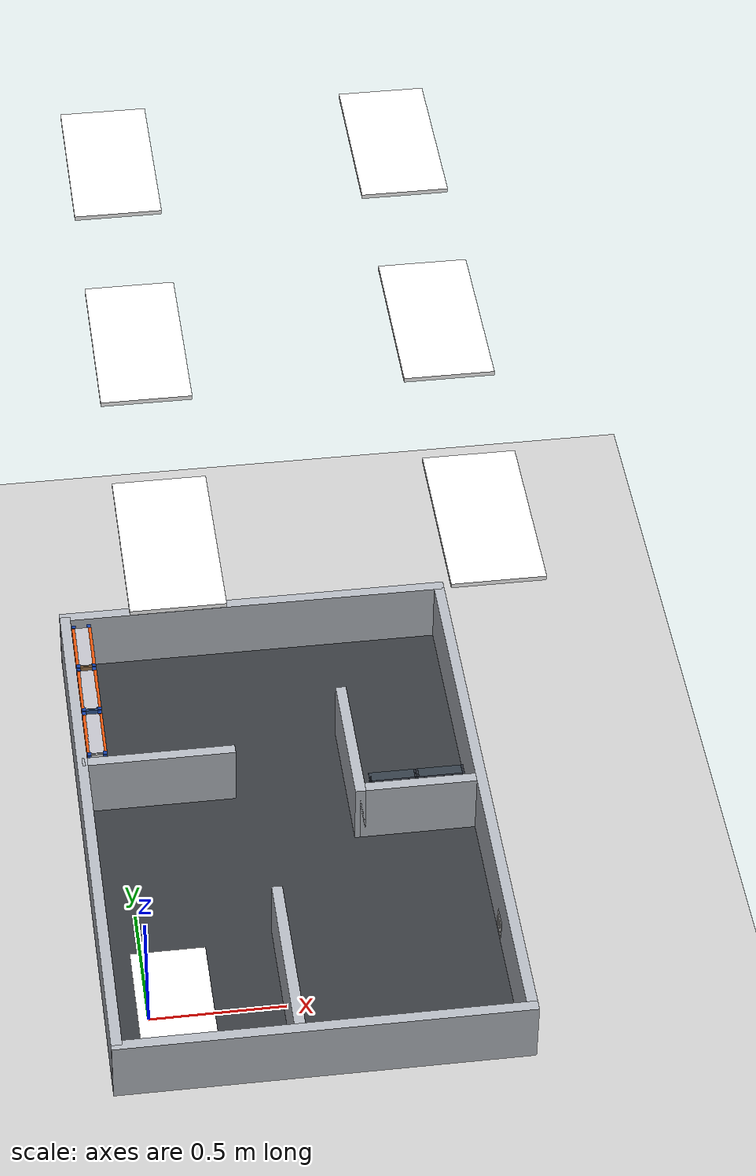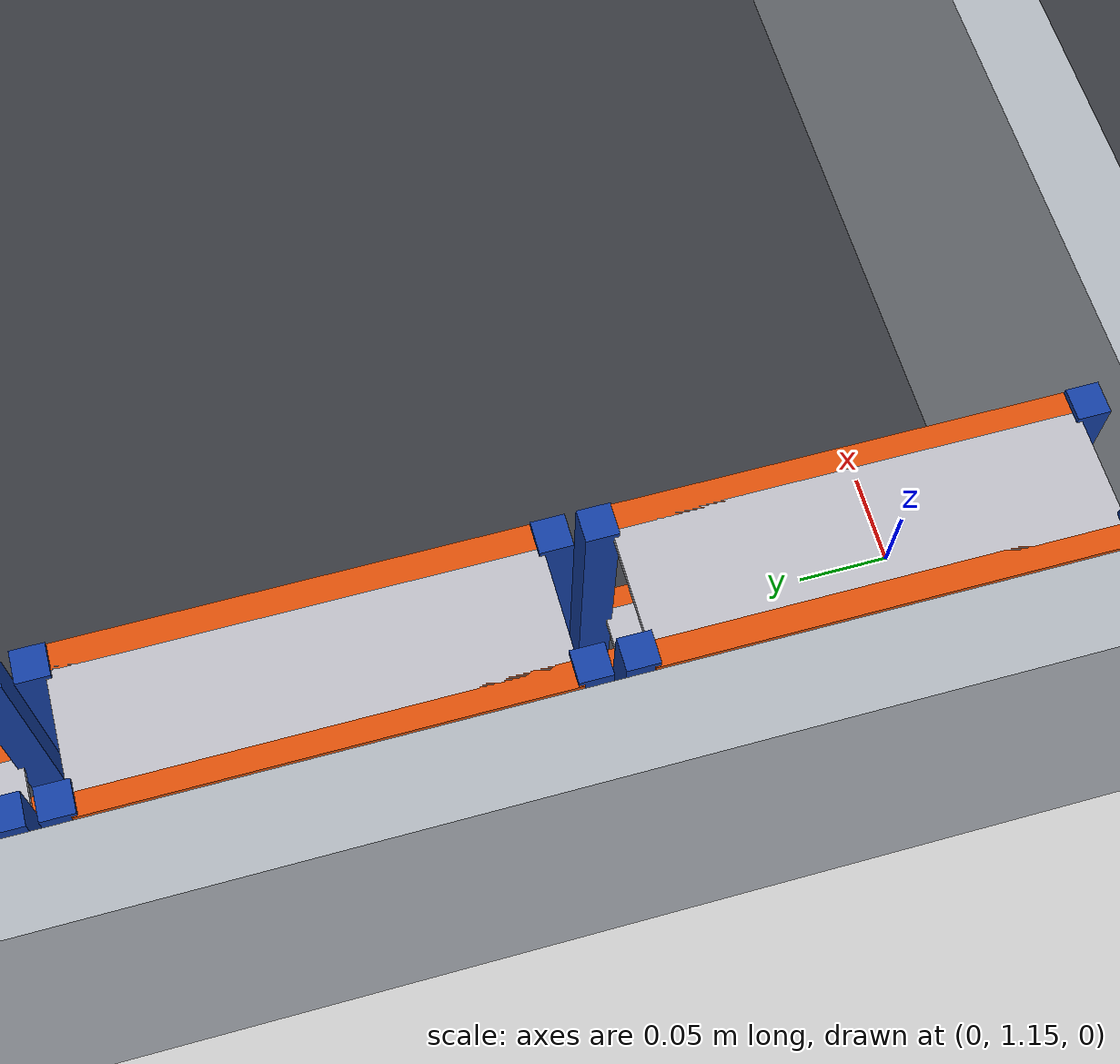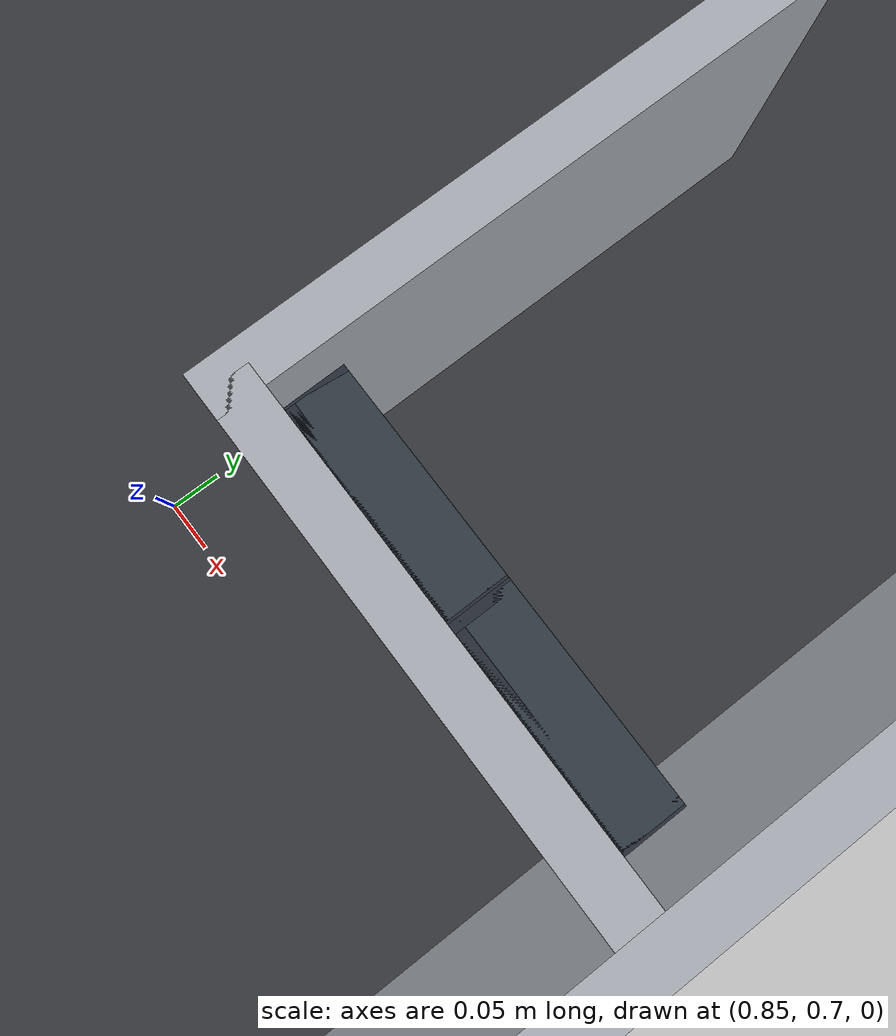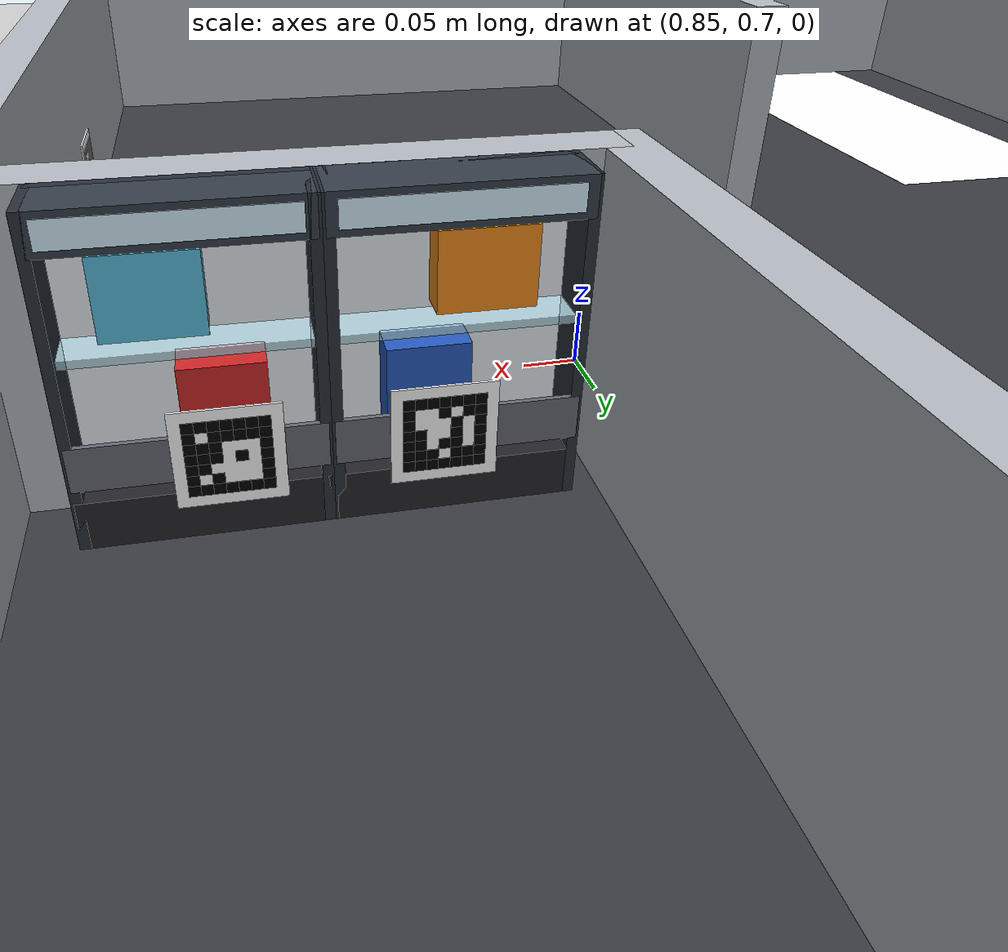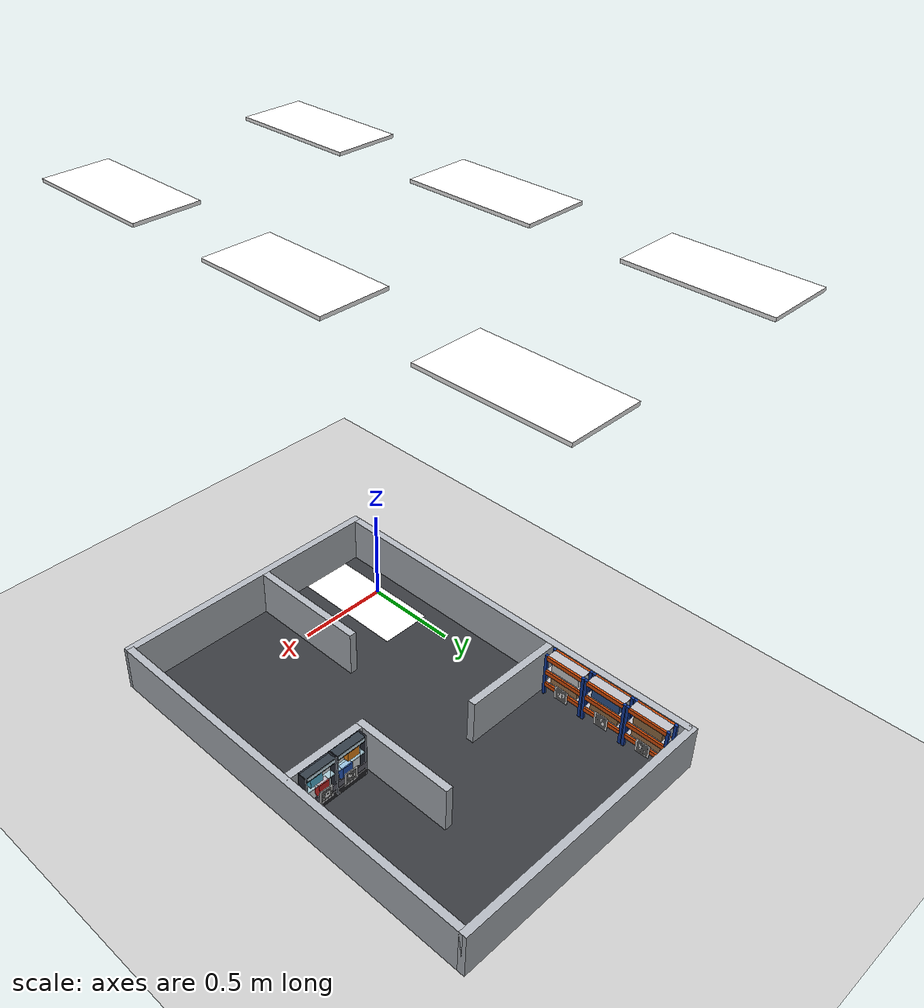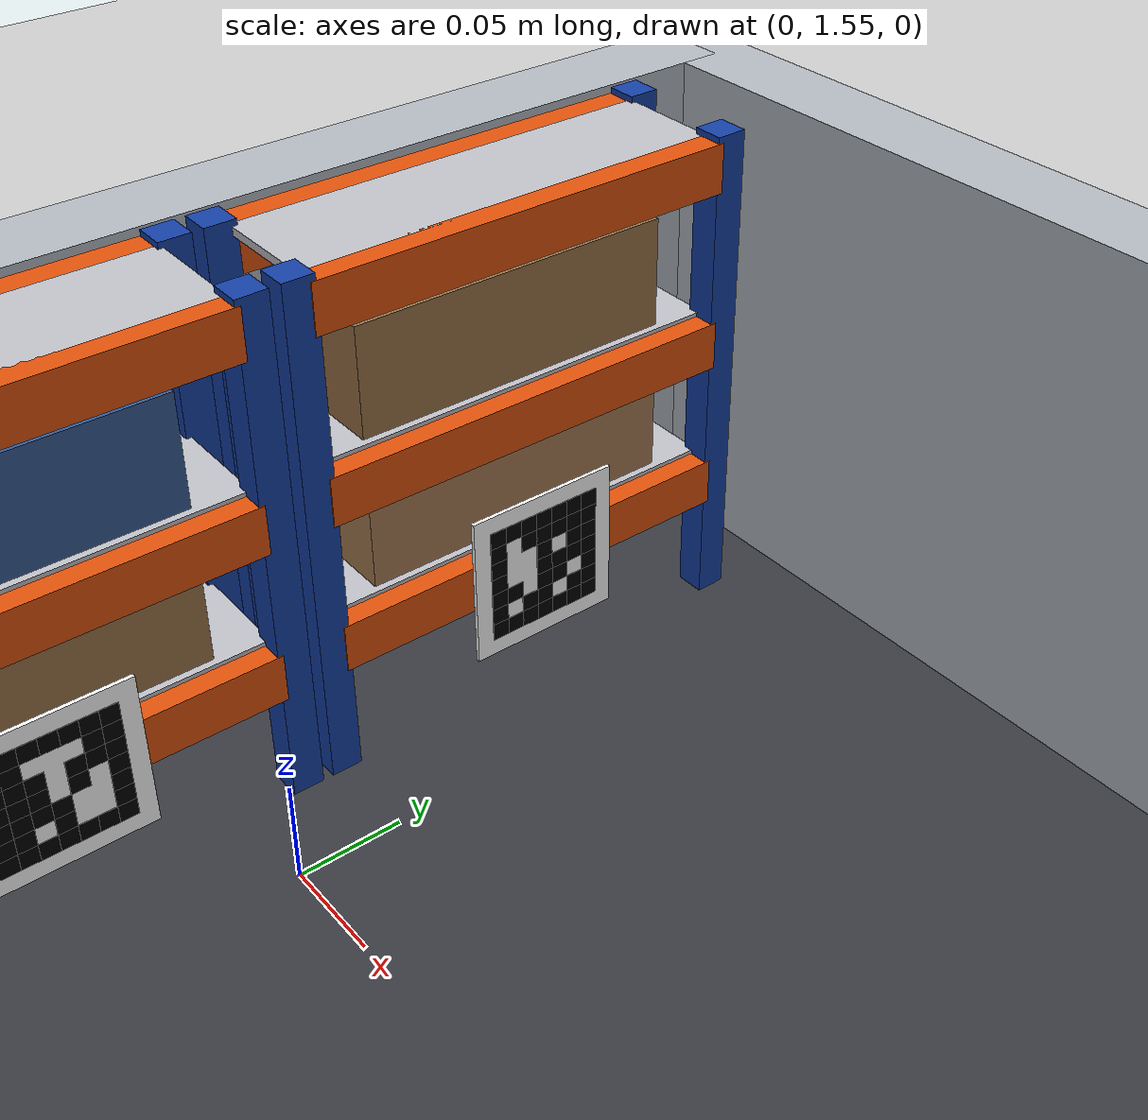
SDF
<sdf version="1.8">
 <world name="default">
  <physics name="1ms" type="ignored">
   <max_step_size>0.001</max_step_size>
   <real_time_factor>1.0</real_time_factor>
  </physics>
  <plugin filename="gz-sim-physics-system" name="gz::sim::systems::Physics"/>
  <plugin filename="gz-sim-sensors-system" name="gz::sim::systems::Sensors">
   <render_engine>ogre2</render_engine>
  </plugin>
  <plugin filename="gz-sim-user-commands-system" name="gz::sim::systems::UserCommands"/>
  <plugin filename="gz-sim-scene-broadcaster-system" name="gz::sim::systems::SceneBroadcaster"/>
  <plugin filename="gz-sim-imu-system" name="gz::sim::systems::Imu"/>
  <light type="directional" name="sun">
   <cast_shadows>false</cast_shadows>
   <pose>0.6 0.8 5 0 0 0</pose>
   <diffuse>0.4 0.4 0.42 1</diffuse>
   <specular>0.1 0.1 0.1 1</specular>
   <direction>0 0 -1</direction>
  </light>
  <light type="point" name="office_light_grid_0">
   <cast_shadows>false</cast_shadows>
   <pose>0.10 -0.22 2.50 0 0 0</pose>
   <diffuse>0.72 0.72 0.75 1</diffuse>
   <specular>0.15 0.15 0.15 1</specular>
   <attenuation>
    <range>6.0</range>
    <constant>0.6</constant>
    <linear>0.15</linear>
    <quadratic>0.03</quadratic>
   </attenuation>
  </light>
  <light type="point" name="office_light_grid_1">
   <cast_shadows>false</cast_shadows>
   <pose>1.10 -0.22 2.50 0 0 0</pose>
   <diffuse>0.72 0.72 0.75 1</diffuse>
   <specular>0.15 0.15 0.15 1</specular>
   <attenuation>
    <range>6.0</range>
    <constant>0.6</constant>
    <linear>0.15</linear>
    <quadratic>0.03</quadratic>
   </attenuation>
  </light>
  <light type="point" name="office_light_grid_2">
   <cast_shadows>false</cast_shadows>
   <pose>0.10 0.78 2.50 0 0 0</pose>
   <diffuse>0.72 0.72 0.75 1</diffuse>
   <specular>0.15 0.15 0.15 1</specular>
   <attenuation>
    <range>6.0</range>
    <constant>0.6</constant>
    <linear>0.15</linear>
    <quadratic>0.03</quadratic>
   </attenuation>
  </light>
  <light type="point" name="office_light_grid_3">
   <cast_shadows>false</cast_shadows>
   <pose>1.10 0.78 2.50 0 0 0</pose>
   <diffuse>0.72 0.72 0.75 1</diffuse>
   <specular>0.15 0.15 0.15 1</specular>
   <attenuation>
    <range>6.0</range>
    <constant>0.6</constant>
    <linear>0.15</linear>
    <quadratic>0.03</quadratic>
   </attenuation>
  </light>
  <light type="point" name="office_light_grid_4">
   <cast_shadows>false</cast_shadows>
   <pose>0.10 1.78 2.50 0 0 0</pose>
   <diffuse>0.72 0.72 0.75 1</diffuse>
   <specular>0.15 0.15 0.15 1</specular>
   <attenuation>
    <range>6.0</range>
    <constant>0.6</constant>
    <linear>0.15</linear>
    <quadratic>0.03</quadratic>
   </attenuation>
  </light>
  <light type="point" name="office_light_grid_5">
   <cast_shadows>false</cast_shadows>
   <pose>1.10 1.78 2.50 0 0 0</pose>
   <diffuse>0.72 0.72 0.75 1</diffuse>
   <specular>0.15 0.15 0.15 1</specular>
   <attenuation>
    <range>6.0</range>
    <constant>0.6</constant>
    <linear>0.15</linear>
    <quadratic>0.03</quadratic>
   </attenuation>
  </light>
  <model name="ground_plane">
   <static>true</static>
   <link name="link">
    <collision name="collision">
     <geometry><plane><normal>0 0 1</normal><size>10 10</size></plane></geometry>
    </collision>
    <visual name="visual">
     <geometry><plane><normal>0 0 1</normal><size>10 10</size></plane></geometry>
     <material><ambient>0.8 0.8 0.8 1</ambient><diffuse>0.8 0.8 0.8 1</diffuse></material>
    </visual>
   </link>
  </model>
  <model name="arena_interior_floor">
   <static>true</static>
   <pose>0.6000 0.7800 0.0005 0 0 0</pose>
   <link name="link">
    <collision name="collision"><geometry><box><size>1.4400 2.1600 0.0010</size></box></geometry></collision>
    <visual name="visual">
     <geometry><box><size>1.4400 2.1600 0.0010</size></box></geometry>
     <material>
      <ambient>0.18 0.18 0.20 1</ambient>
      <diffuse>0.22 0.23 0.25 1</diffuse>
      <specular>0.12 0.12 0.12 1</specular>
     </material>
    </visual>
   </link>
  </model>
  <model name="office_ceiling_fixtures">
   <static>true</static>
   <link name="link">
    <visual name="troffer_0">
     <pose>0.10 -0.22 2.505 0 0 0</pose>
     <geometry><box><size>0.30 0.60 0.015</size></box></geometry>
     <material><ambient>1 1 1 1</ambient><diffuse>1 1 1 1</diffuse><emissive>0.9 0.9 0.95 1</emissive></material>
    </visual>
    <visual name="troffer_1">
     <pose>1.10 -0.22 2.505 0 0 0</pose>
     <geometry><box><size>0.30 0.60 0.015</size></box></geometry>
     <material><ambient>1 1 1 1</ambient><diffuse>1 1 1 1</diffuse><emissive>0.9 0.9 0.95 1</emissive></material>
    </visual>
    <visual name="troffer_2">
     <pose>0.10 0.78 2.505 0 0 0</pose>
     <geometry><box><size>0.30 0.60 0.015</size></box></geometry>
     <material><ambient>1 1 1 1</ambient><diffuse>1 1 1 1</diffuse><emissive>0.9 0.9 0.95 1</emissive></material>
    </visual>
    <visual name="troffer_3">
     <pose>1.10 0.78 2.505 0 0 0</pose>
     <geometry><box><size>0.30 0.60 0.015</size></box></geometry>
     <material><ambient>1 1 1 1</ambient><diffuse>1 1 1 1</diffuse><emissive>0.9 0.9 0.95 1</emissive></material>
    </visual>
    <visual name="troffer_4">
     <pose>0.10 1.78 2.505 0 0 0</pose>
     <geometry><box><size>0.30 0.60 0.015</size></box></geometry>
     <material><ambient>1 1 1 1</ambient><diffuse>1 1 1 1</diffuse><emissive>0.9 0.9 0.95 1</emissive></material>
    </visual>
    <visual name="troffer_5">
     <pose>1.10 1.78 2.505 0 0 0</pose>
     <geometry><box><size>0.30 0.60 0.015</size></box></geometry>
     <material><ambient>1 1 1 1</ambient><diffuse>1 1 1 1</diffuse><emissive>0.9 0.9 0.95 1</emissive></material>
    </visual>
   </link>
  </model>
  <model name="wall_north">
   <static>true</static>
   <pose>0.6000 1.8800 0.1250 0 0 0</pose>
   <link name="link">
    <collision name="collision"><geometry><box><size>1.5200 0.0400 0.2500</size></box></geometry></collision>
    <visual name="visual">
     <geometry><box><size>1.5200 0.0400 0.2500</size></box></geometry>
     <material>
      <ambient>0.7 0.72 0.75 1</ambient>
      <diffuse>0.7 0.72 0.75 1</diffuse>
      <specular>0.1 0.1 0.1 1</specular>
     </material>
    </visual>
   </link>
  </model>
  <model name="wall_south">
   <static>true</static>
   <pose>0.6000 -0.3200 0.1250 0 0 0</pose>
   <link name="link">
    <collision name="collision"><geometry><box><size>1.5200 0.0400 0.2500</size></box></geometry></collision>
    <visual name="visual">
     <geometry><box><size>1.5200 0.0400 0.2500</size></box></geometry>
     <material>
      <ambient>0.7 0.72 0.75 1</ambient>
      <diffuse>0.7 0.72 0.75 1</diffuse>
      <specular>0.1 0.1 0.1 1</specular>
     </material>
    </visual>
   </link>
  </model>
  <model name="wall_west">
   <static>true</static>
   <pose>-0.1400 0.7800 0.1250 0 0 0</pose>
   <link name="link">
    <collision name="collision"><geometry><box><size>0.0400 2.2000 0.2500</size></box></geometry></collision>
    <visual name="visual">
     <geometry><box><size>0.0400 2.2000 0.2500</size></box></geometry>
     <material>
      <ambient>0.7 0.72 0.75 1</ambient>
      <diffuse>0.7 0.72 0.75 1</diffuse>
      <specular>0.1 0.1 0.1 1</specular>
     </material>
    </visual>
   </link>
  </model>
  <model name="wall_east">
   <static>true</static>
   <pose>1.3400 0.7800 0.1250 0 0 0</pose>
   <link name="link">
    <collision name="collision"><geometry><box><size>0.0400 2.2000 0.2500</size></box></geometry></collision>
    <visual name="visual">
     <geometry><box><size>0.0400 2.2000 0.2500</size></box></geometry>
     <material>
      <ambient>0.7 0.72 0.75 1</ambient>
      <diffuse>0.7 0.72 0.75 1</diffuse>
      <specular>0.1 0.1 0.1 1</specular>
     </material>
    </visual>
   </link>
  </model>
  <model name="wall_shelf1_divider">
   <static>true</static>
   <pose>0.1500 1.0800 0.1250 0 0 0</pose>
   <link name="link">
    <collision name="collision"><geometry><box><size>0.5800 0.0400 0.2500</size></box></geometry></collision>
    <visual name="visual">
     <geometry><box><size>0.5800 0.0400 0.2500</size></box></geometry>
     <material>
      <ambient>0.7 0.72 0.75 1</ambient>
      <diffuse>0.7 0.72 0.75 1</diffuse>
      <specular>0.1 0.1 0.1 1</specular>
     </material>
    </visual>
   </link>
  </model>
  <model name="wall_center_pillar">
   <static>true</static>
   <pose>0.5100 0.0300 0.1250 0 0 0</pose>
   <link name="link">
    <collision name="collision"><geometry><box><size>0.0400 0.6600 0.2500</size></box></geometry></collision>
    <visual name="visual">
     <geometry><box><size>0.0400 0.6600 0.2500</size></box></geometry>
     <material>
      <ambient>0.7 0.72 0.75 1</ambient>
      <diffuse>0.7 0.72 0.75 1</diffuse>
      <specular>0.1 0.1 0.1 1</specular>
     </material>
    </visual>
   </link>
  </model>
  <model name="wall_shelf2_divider">
   <static>true</static>
   <pose>0.8800 1.0800 0.1250 0 0 0</pose>
   <link name="link">
    <collision name="collision"><geometry><box><size>0.0400 0.5600 0.2500</size></box></geometry></collision>
    <visual name="visual">
     <geometry><box><size>0.0400 0.5600 0.2500</size></box></geometry>
     <material>
      <ambient>0.7 0.72 0.75 1</ambient>
      <diffuse>0.7 0.72 0.75 1</diffuse>
      <specular>0.1 0.1 0.1 1</specular>
     </material>
    </visual>
   </link>
  </model>
  <model name="wall_shelf2_back">
   <static>true</static>
   <pose>1.1100 0.8200 0.1250 0 0 0</pose>
   <link name="link">
    <collision name="collision"><geometry><box><size>0.4600 0.0400 0.2500</size></box></geometry></collision>
    <visual name="visual">
     <geometry><box><size>0.4600 0.0400 0.2500</size></box></geometry>
     <material>
      <ambient>0.7 0.72 0.75 1</ambient>
      <diffuse>0.7 0.72 0.75 1</diffuse>
      <specular>0.1 0.1 0.1 1</specular>
     </material>
    </visual>
   </link>
  </model>
  <model name="shelf1_costco_rack_left">
   <static>true</static>
   <pose>-0.0800 1.2300 0.1250 0 0 0</pose>
   <link name="link">
    <collision name="collision"><geometry><box><size>0.0700 0.2300 0.2500</size></box></geometry></collision>
    <visual name="post_FL">
     <pose>0.0300 -0.110 0 0 0 0</pose>
     <geometry><box><size>0.015 0.015 0.25</size></box></geometry>
     <material>
      <ambient>0.05 0.15 0.45 1</ambient>
      <diffuse>0.08 0.25 0.65 1</diffuse>
      <specular>0.3 0.3 0.4 1</specular>
     </material>
    </visual>
    <visual name="post_FR">
     <pose>0.0300 0.110 0 0 0 0</pose>
     <geometry><box><size>0.015 0.015 0.25</size></box></geometry>
     <material>
      <ambient>0.05 0.15 0.45 1</ambient>
      <diffuse>0.08 0.25 0.65 1</diffuse>
      <specular>0.3 0.3 0.4 1</specular>
     </material>
    </visual>
    <visual name="post_RL">
     <pose>-0.0300 -0.110 0 0 0 0</pose>
     <geometry><box><size>0.015 0.015 0.25</size></box></geometry>
     <material>
      <ambient>0.05 0.15 0.45 1</ambient>
      <diffuse>0.08 0.25 0.65 1</diffuse>
      <specular>0.3 0.3 0.4 1</specular>
     </material>
    </visual>
    <visual name="post_RR">
     <pose>-0.0300 0.110 0 0 0 0</pose>
     <geometry><box><size>0.015 0.015 0.25</size></box></geometry>
     <material>
      <ambient>0.05 0.15 0.45 1</ambient>
      <diffuse>0.08 0.25 0.65 1</diffuse>
      <specular>0.3 0.3 0.4 1</specular>
     </material>
    </visual>
    <visual name="t1_beam_F">
     <pose>0.0320 0 -0.057 0 0 0</pose>
     <geometry><box><size>0.012 0.21 0.024</size></box></geometry>
     <material>
      <ambient>0.6 0.2 0.02 1</ambient>
      <diffuse>0.88 0.32 0.04 1</diffuse>
      <specular>0.4 0.2 0.1 1</specular>
     </material>
    </visual>
    <visual name="t1_beam_R">
     <pose>-0.0320 0 -0.057 0 0 0</pose>
     <geometry><box><size>0.012 0.21 0.024</size></box></geometry>
     <material><ambient>0.6 0.2 0.02 1</ambient><diffuse>0.88 0.32 0.04 1</diffuse></material>
    </visual>
    <visual name="t1_deck">
     <pose>0 0 -0.045 0 0 0</pose>
     <geometry><box><size>0.055 0.21 0.004</size></box></geometry>
     <material><ambient>0.65 0.65 0.68 1</ambient><diffuse>0.75 0.75 0.78 1</diffuse></material>
    </visual>
    <visual name="t1_box">
     <pose>0 0 -0.016 0 0 0</pose>
     <geometry><box><size>0.048 0.16 0.054</size></box></geometry>
     <material><ambient>0.55 0.40 0.25 1</ambient><diffuse>0.65 0.48 0.32 1</diffuse></material>
    </visual>
    <visual name="t2_beam_F">
     <pose>0.0320 0 0.020 0 0 0</pose>
     <geometry><box><size>0.012 0.21 0.024</size></box></geometry>
     <material>
      <ambient>0.6 0.2 0.02 1</ambient>
      <diffuse>0.88 0.32 0.04 1</diffuse>
      <specular>0.4 0.2 0.1 1</specular>
     </material>
    </visual>
    <visual name="t2_beam_R">
     <pose>-0.0320 0 0.020 0 0 0</pose>
     <geometry><box><size>0.012 0.21 0.024</size></box></geometry>
     <material><ambient>0.6 0.2 0.02 1</ambient><diffuse>0.88 0.32 0.04 1</diffuse></material>
    </visual>
    <visual name="t2_deck">
     <pose>0 0 0.032 0 0 0</pose>
     <geometry><box><size>0.055 0.21 0.004</size></box></geometry>
     <material><ambient>0.65 0.65 0.68 1</ambient><diffuse>0.75 0.75 0.78 1</diffuse></material>
    </visual>
    <visual name="t2_box">
     <pose>0 0 0.061 0 0 0</pose>
     <geometry><box><size>0.048 0.16 0.054</size></box></geometry>
     <material><ambient>0.75 0.75 0.75 1</ambient><diffuse>0.85 0.85 0.85 1</diffuse></material>
    </visual>
    <visual name="t3_beam_F">
     <pose>0.0320 0 0.110 0 0 0</pose>
     <geometry><box><size>0.012 0.21 0.024</size></box></geometry>
     <material>
      <ambient>0.6 0.2 0.02 1</ambient>
      <diffuse>0.88 0.32 0.04 1</diffuse>
      <specular>0.4 0.2 0.1 1</specular>
     </material>
    </visual>
    <visual name="t3_beam_R">
     <pose>-0.0320 0 0.110 0 0 0</pose>
     <geometry><box><size>0.012 0.21 0.024</size></box></geometry>
     <material><ambient>0.6 0.2 0.02 1</ambient><diffuse>0.88 0.32 0.04 1</diffuse></material>
    </visual>
    <visual name="t3_deck">
     <pose>0 0 0.120 0 0 0</pose>
     <geometry><box><size>0.055 0.21 0.004</size></box></geometry>
     <material><ambient>0.65 0.65 0.68 1</ambient><diffuse>0.75 0.75 0.78 1</diffuse></material>
    </visual>
   </link>
  </model>
  <model name="shelf1_costco_rack_center">
   <static>true</static>
   <pose>-0.0800 1.4700 0.1250 0 0 0</pose>
   <link name="link">
    <collision name="collision"><geometry><box><size>0.0700 0.2300 0.2500</size></box></geometry></collision>
    <visual name="post_FL">
     <pose>0.0300 -0.110 0 0 0 0</pose>
     <geometry><box><size>0.015 0.015 0.25</size></box></geometry>
     <material>
      <ambient>0.05 0.15 0.45 1</ambient>
      <diffuse>0.08 0.25 0.65 1</diffuse>
      <specular>0.3 0.3 0.4 1</specular>
     </material>
    </visual>
    <visual name="post_FR">
     <pose>0.0300 0.110 0 0 0 0</pose>
     <geometry><box><size>0.015 0.015 0.25</size></box></geometry>
     <material>
      <ambient>0.05 0.15 0.45 1</ambient>
      <diffuse>0.08 0.25 0.65 1</diffuse>
      <specular>0.3 0.3 0.4 1</specular>
     </material>
    </visual>
    <visual name="post_RL">
     <pose>-0.0300 -0.110 0 0 0 0</pose>
     <geometry><box><size>0.015 0.015 0.25</size></box></geometry>
     <material>
      <ambient>0.05 0.15 0.45 1</ambient>
      <diffuse>0.08 0.25 0.65 1</diffuse>
      <specular>0.3 0.3 0.4 1</specular>
     </material>
    </visual>
    <visual name="post_RR">
     <pose>-0.0300 0.110 0 0 0 0</pose>
     <geometry><box><size>0.015 0.015 0.25</size></box></geometry>
     <material>
      <ambient>0.05 0.15 0.45 1</ambient>
      <diffuse>0.08 0.25 0.65 1</diffuse>
      <specular>0.3 0.3 0.4 1</specular>
     </material>
    </visual>
    <visual name="t1_beam_F">
     <pose>0.0320 0 -0.057 0 0 0</pose>
     <geometry><box><size>0.012 0.21 0.024</size></box></geometry>
     <material>
      <ambient>0.6 0.2 0.02 1</ambient>
      <diffuse>0.88 0.32 0.04 1</diffuse>
      <specular>0.4 0.2 0.1 1</specular>
     </material>
    </visual>
    <visual name="t1_beam_R">
     <pose>-0.0320 0 -0.057 0 0 0</pose>
     <geometry><box><size>0.012 0.21 0.024</size></box></geometry>
     <material><ambient>0.6 0.2 0.02 1</ambient><diffuse>0.88 0.32 0.04 1</diffuse></material>
    </visual>
    <visual name="t1_deck">
     <pose>0 0 -0.045 0 0 0</pose>
     <geometry><box><size>0.055 0.21 0.004</size></box></geometry>
     <material><ambient>0.65 0.65 0.68 1</ambient><diffuse>0.75 0.75 0.78 1</diffuse></material>
    </visual>
    <visual name="t1_box">
     <pose>0 0 -0.016 0 0 0</pose>
     <geometry><box><size>0.048 0.16 0.054</size></box></geometry>
     <material><ambient>0.50 0.36 0.22 1</ambient><diffuse>0.60 0.44 0.28 1</diffuse></material>
    </visual>
    <visual name="t2_beam_F">
     <pose>0.0320 0 0.020 0 0 0</pose>
     <geometry><box><size>0.012 0.21 0.024</size></box></geometry>
     <material>
      <ambient>0.6 0.2 0.02 1</ambient>
      <diffuse>0.88 0.32 0.04 1</diffuse>
      <specular>0.4 0.2 0.1 1</specular>
     </material>
    </visual>
    <visual name="t2_beam_R">
     <pose>-0.0320 0 0.020 0 0 0</pose>
     <geometry><box><size>0.012 0.21 0.024</size></box></geometry>
     <material><ambient>0.6 0.2 0.02 1</ambient><diffuse>0.88 0.32 0.04 1</diffuse></material>
    </visual>
    <visual name="t2_deck">
     <pose>0 0 0.032 0 0 0</pose>
     <geometry><box><size>0.055 0.21 0.004</size></box></geometry>
     <material><ambient>0.65 0.65 0.68 1</ambient><diffuse>0.75 0.75 0.78 1</diffuse></material>
    </visual>
    <visual name="t2_box">
     <pose>0 0 0.061 0 0 0</pose>
     <geometry><box><size>0.048 0.16 0.054</size></box></geometry>
     <material><ambient>0.15 0.28 0.48 1</ambient><diffuse>0.20 0.35 0.58 1</diffuse></material>
    </visual>
    <visual name="t3_beam_F">
     <pose>0.0320 0 0.110 0 0 0</pose>
     <geometry><box><size>0.012 0.21 0.024</size></box></geometry>
     <material>
      <ambient>0.6 0.2 0.02 1</ambient>
      <diffuse>0.88 0.32 0.04 1</diffuse>
      <specular>0.4 0.2 0.1 1</specular>
     </material>
    </visual>
    <visual name="t3_beam_R">
     <pose>-0.0320 0 0.110 0 0 0</pose>
     <geometry><box><size>0.012 0.21 0.024</size></box></geometry>
     <material><ambient>0.6 0.2 0.02 1</ambient><diffuse>0.88 0.32 0.04 1</diffuse></material>
    </visual>
    <visual name="t3_deck">
     <pose>0 0 0.120 0 0 0</pose>
     <geometry><box><size>0.055 0.21 0.004</size></box></geometry>
     <material><ambient>0.65 0.65 0.68 1</ambient><diffuse>0.75 0.75 0.78 1</diffuse></material>
    </visual>
   </link>
  </model>
  <model name="shelf1_costco_rack_right">
   <static>true</static>
   <pose>-0.0800 1.7100 0.1250 0 0 0</pose>
   <link name="link">
    <collision name="collision"><geometry><box><size>0.0700 0.2300 0.2500</size></box></geometry></collision>
    <visual name="post_FL">
     <pose>0.0300 -0.110 0 0 0 0</pose>
     <geometry><box><size>0.015 0.015 0.25</size></box></geometry>
     <material>
      <ambient>0.05 0.15 0.45 1</ambient>
      <diffuse>0.08 0.25 0.65 1</diffuse>
      <specular>0.3 0.3 0.4 1</specular>
     </material>
    </visual>
    <visual name="post_FR">
     <pose>0.0300 0.110 0 0 0 0</pose>
     <geometry><box><size>0.015 0.015 0.25</size></box></geometry>
     <material>
      <ambient>0.05 0.15 0.45 1</ambient>
      <diffuse>0.08 0.25 0.65 1</diffuse>
      <specular>0.3 0.3 0.4 1</specular>
     </material>
    </visual>
    <visual name="post_RL">
     <pose>-0.0300 -0.110 0 0 0 0</pose>
     <geometry><box><size>0.015 0.015 0.25</size></box></geometry>
     <material>
      <ambient>0.05 0.15 0.45 1</ambient>
      <diffuse>0.08 0.25 0.65 1</diffuse>
      <specular>0.3 0.3 0.4 1</specular>
     </material>
    </visual>
    <visual name="post_RR">
     <pose>-0.0300 0.110 0 0 0 0</pose>
     <geometry><box><size>0.015 0.015 0.25</size></box></geometry>
     <material>
      <ambient>0.05 0.15 0.45 1</ambient>
      <diffuse>0.08 0.25 0.65 1</diffuse>
      <specular>0.3 0.3 0.4 1</specular>
     </material>
    </visual>
    <visual name="t1_beam_F">
     <pose>0.0320 0 -0.057 0 0 0</pose>
     <geometry><box><size>0.012 0.21 0.024</size></box></geometry>
     <material>
      <ambient>0.6 0.2 0.02 1</ambient>
      <diffuse>0.88 0.32 0.04 1</diffuse>
      <specular>0.4 0.2 0.1 1</specular>
     </material>
    </visual>
    <visual name="t1_beam_R">
     <pose>-0.0320 0 -0.057 0 0 0</pose>
     <geometry><box><size>0.012 0.21 0.024</size></box></geometry>
     <material><ambient>0.6 0.2 0.02 1</ambient><diffuse>0.88 0.32 0.04 1</diffuse></material>
    </visual>
    <visual name="t1_deck">
     <pose>0 0 -0.045 0 0 0</pose>
     <geometry><box><size>0.055 0.21 0.004</size></box></geometry>
     <material><ambient>0.65 0.65 0.68 1</ambient><diffuse>0.75 0.75 0.78 1</diffuse></material>
    </visual>
    <visual name="t1_box">
     <pose>0 0 -0.016 0 0 0</pose>
     <geometry><box><size>0.048 0.16 0.054</size></box></geometry>
     <material><ambient>0.55 0.40 0.25 1</ambient><diffuse>0.65 0.48 0.32 1</diffuse></material>
    </visual>
    <visual name="t2_beam_F">
     <pose>0.0320 0 0.020 0 0 0</pose>
     <geometry><box><size>0.012 0.21 0.024</size></box></geometry>
     <material>
      <ambient>0.6 0.2 0.02 1</ambient>
      <diffuse>0.88 0.32 0.04 1</diffuse>
      <specular>0.4 0.2 0.1 1</specular>
     </material>
    </visual>
    <visual name="t2_beam_R">
     <pose>-0.0320 0 0.020 0 0 0</pose>
     <geometry><box><size>0.012 0.21 0.024</size></box></geometry>
     <material><ambient>0.6 0.2 0.02 1</ambient><diffuse>0.88 0.32 0.04 1</diffuse></material>
    </visual>
    <visual name="t2_deck">
     <pose>0 0 0.032 0 0 0</pose>
     <geometry><box><size>0.055 0.21 0.004</size></box></geometry>
     <material><ambient>0.65 0.65 0.68 1</ambient><diffuse>0.75 0.75 0.78 1</diffuse></material>
    </visual>
    <visual name="t2_box">
     <pose>0 0 0.061 0 0 0</pose>
     <geometry><box><size>0.048 0.16 0.054</size></box></geometry>
     <material><ambient>0.50 0.36 0.22 1</ambient><diffuse>0.60 0.44 0.28 1</diffuse></material>
    </visual>
    <visual name="t3_beam_F">
     <pose>0.0320 0 0.110 0 0 0</pose>
     <geometry><box><size>0.012 0.21 0.024</size></box></geometry>
     <material>
      <ambient>0.6 0.2 0.02 1</ambient>
      <diffuse>0.88 0.32 0.04 1</diffuse>
      <specular>0.4 0.2 0.1 1</specular>
     </material>
    </visual>
    <visual name="t3_beam_R">
     <pose>-0.0320 0 0.110 0 0 0</pose>
     <geometry><box><size>0.012 0.21 0.024</size></box></geometry>
     <material><ambient>0.6 0.2 0.02 1</ambient><diffuse>0.88 0.32 0.04 1</diffuse></material>
    </visual>
    <visual name="t3_deck">
     <pose>0 0 0.120 0 0 0</pose>
     <geometry><box><size>0.055 0.21 0.004</size></box></geometry>
     <material><ambient>0.65 0.65 0.68 1</ambient><diffuse>0.75 0.75 0.78 1</diffuse></material>
    </visual>
   </link>
  </model>
  <model name="shelf2_supermarket_cooler_1">
   <static>true</static>
   <pose>1.0100 0.8650 0.1250 0 0 0</pose>
   <link name="link">
    <collision name="collision"><geometry><box><size>0.1800 0.0500 0.2500</size></box></geometry></collision>
    <visual name="back">
     <pose>0 -0.021 0 0 0 0</pose>
     <geometry><box><size>0.176 0.008 0.250</size></box></geometry>
     <material>
      <ambient>0.12 0.14 0.16 1</ambient>
      <diffuse>0.16 0.18 0.22 1</diffuse>
      <specular>0.3 0.3 0.3 1</specular>
     </material>
    </visual>
    <visual name="side_L">
     <pose>-0.086 0 0 0 0 0</pose>
     <geometry><box><size>0.008 0.050 0.250</size></box></geometry>
     <material><ambient>0.12 0.14 0.16 1</ambient><diffuse>0.16 0.18 0.22 1</diffuse></material>
    </visual>
    <visual name="side_R">
     <pose>0.086 0 0 0 0 0</pose>
     <geometry><box><size>0.008 0.050 0.250</size></box></geometry>
     <material><ambient>0.12 0.14 0.16 1</ambient><diffuse>0.16 0.18 0.22 1</diffuse></material>
    </visual>
    <visual name="kickplate">
     <pose>0 0 -0.105 0 0 0</pose>
     <geometry><box><size>0.176 0.050 0.040</size></box></geometry>
     <material><ambient>0.10 0.10 0.12 1</ambient><diffuse>0.14 0.14 0.16 1</diffuse></material>
    </visual>
    <visual name="canopy">
     <pose>0 0 0.110 0 0 0</pose>
     <geometry><box><size>0.176 0.050 0.030</size></box></geometry>
     <material><ambient>0.15 0.18 0.22 1</ambient><diffuse>0.20 0.24 0.28 1</diffuse></material>
    </visual>
    <visual name="top_light">
     <pose>0 0.024 0.110 0 0 0</pose>
     <geometry><box><size>0.160 0.003 0.020</size></box></geometry>
     <material>
      <ambient>0.7 0.9 1 1</ambient>
      <diffuse>0.85 0.95 1 1</diffuse>
      <emissive>0.7 0.9 1 1</emissive>
     </material>
    </visual>
    <visual name="lining">
     <pose>0 -0.015 0 0 0 0</pose>
     <geometry><box><size>0.164 0.005 0.180</size></box></geometry>
     <material><ambient>0.85 0.88 0.90 1</ambient><diffuse>0.92 0.94 0.96 1</diffuse></material>
    </visual>
    <visual name="price_rail">
     <pose>0 0.024 -0.057 0 0 0</pose>
     <geometry><box><size>0.176 0.004 0.035</size></box></geometry>
     <material>
      <ambient>0.3 0.3 0.35 1</ambient>
      <diffuse>0.4 0.4 0.45 1</diffuse>
      <specular>0.5 0.5 0.5 1</specular>
     </material>
    </visual>
    <visual name="glass_shelf">
     <pose>0 0.002 0.020 0 0 0</pose>
     <geometry><box><size>0.164 0.035 0.006</size></box></geometry>
     <material><ambient>0.7 0.85 0.9 0.8</ambient><diffuse>0.75 0.90 0.95 0.8</diffuse></material>
    </visual>
    <visual name="dairy_1">
     <pose>0.02 0.002 -0.030 0 0 0</pose>
     <geometry><box><size>0.060 0.030 0.075</size></box></geometry>
     <material><ambient>0.10 0.25 0.65 1</ambient><diffuse>0.15 0.35 0.75 1</diffuse></material>
    </visual>
    <visual name="drink_1">
     <pose>-0.02 0.002 0.060 0 0 0</pose>
     <geometry><box><size>0.070 0.025 0.060</size></box></geometry>
     <material><ambient>0.70 0.40 0.05 1</ambient><diffuse>0.95 0.55 0.10 1</diffuse></material>
    </visual>
   </link>
  </model>
  <model name="shelf2_supermarket_cooler_2">
   <static>true</static>
   <pose>1.1900 0.8650 0.1250 0 0 0</pose>
   <link name="link">
    <collision name="collision"><geometry><box><size>0.1800 0.0500 0.2500</size></box></geometry></collision>
    <visual name="back">
     <pose>0 -0.021 0 0 0 0</pose>
     <geometry><box><size>0.176 0.008 0.250</size></box></geometry>
     <material>
      <ambient>0.12 0.14 0.16 1</ambient>
      <diffuse>0.16 0.18 0.22 1</diffuse>
      <specular>0.3 0.3 0.3 1</specular>
     </material>
    </visual>
    <visual name="side_L">
     <pose>-0.086 0 0 0 0 0</pose>
     <geometry><box><size>0.008 0.050 0.250</size></box></geometry>
     <material><ambient>0.12 0.14 0.16 1</ambient><diffuse>0.16 0.18 0.22 1</diffuse></material>
    </visual>
    <visual name="side_R">
     <pose>0.086 0 0 0 0 0</pose>
     <geometry><box><size>0.008 0.050 0.250</size></box></geometry>
     <material><ambient>0.12 0.14 0.16 1</ambient><diffuse>0.16 0.18 0.22 1</diffuse></material>
    </visual>
    <visual name="kickplate">
     <pose>0 0 -0.105 0 0 0</pose>
     <geometry><box><size>0.176 0.050 0.040</size></box></geometry>
     <material><ambient>0.10 0.10 0.12 1</ambient><diffuse>0.14 0.14 0.16 1</diffuse></material>
    </visual>
    <visual name="canopy">
     <pose>0 0 0.110 0 0 0</pose>
     <geometry><box><size>0.176 0.050 0.030</size></box></geometry>
     <material><ambient>0.15 0.18 0.22 1</ambient><diffuse>0.20 0.24 0.28 1</diffuse></material>
    </visual>
    <visual name="top_light">
     <pose>0 0.024 0.110 0 0 0</pose>
     <geometry><box><size>0.160 0.003 0.020</size></box></geometry>
     <material>
      <ambient>0.7 0.9 1 1</ambient>
      <diffuse>0.85 0.95 1 1</diffuse>
      <emissive>0.7 0.9 1 1</emissive>
     </material>
    </visual>
    <visual name="lining">
     <pose>0 -0.015 0 0 0 0</pose>
     <geometry><box><size>0.164 0.005 0.180</size></box></geometry>
     <material><ambient>0.85 0.88 0.90 1</ambient><diffuse>0.92 0.94 0.96 1</diffuse></material>
    </visual>
    <visual name="price_rail">
     <pose>0 0.024 -0.057 0 0 0</pose>
     <geometry><box><size>0.176 0.004 0.035</size></box></geometry>
     <material>
      <ambient>0.3 0.3 0.35 1</ambient>
      <diffuse>0.4 0.4 0.45 1</diffuse>
      <specular>0.5 0.5 0.5 1</specular>
     </material>
    </visual>
    <visual name="glass_shelf">
     <pose>0 0.002 0.020 0 0 0</pose>
     <geometry><box><size>0.164 0.035 0.006</size></box></geometry>
     <material><ambient>0.7 0.85 0.9 0.8</ambient><diffuse>0.75 0.90 0.95 0.8</diffuse></material>
    </visual>
    <visual name="dairy_2">
     <pose>-0.02 0.002 -0.030 0 0 0</pose>
     <geometry><box><size>0.060 0.030 0.075</size></box></geometry>
     <material><ambient>0.60 0.10 0.10 1</ambient><diffuse>0.80 0.15 0.15 1</diffuse></material>
    </visual>
    <visual name="drink_2">
     <pose>0.02 0.002 0.060 0 0 0</pose>
     <geometry><box><size>0.070 0.025 0.060</size></box></geometry>
     <material><ambient>0.25 0.60 0.75 1</ambient><diffuse>0.35 0.75 0.88 1</diffuse></material>
    </visual>
   </link>
  </model>
  <model name="aruco_5x5_id6_shelf1_left">
   <static>true</static>
   <pose>-0.0390 1.2300 0.0680 0.0000 0.0000 3.1416</pose>
   <link name="link">
    <visual name="white_bg">
     <geometry><box><size>0.002 0.07714 0.07714</size></box></geometry>
     <material>
      <ambient>1 1 1 1</ambient>
      <diffuse>1 1 1 1</diffuse>
      <specular>0 0 0 1</specular>
      <emissive>0.92 0.92 0.92 1</emissive>
     </material>
    </visual>
    <visual name="cell_0_0">
     <pose>-0.0008 0.02571 0.02571 0 0 0</pose>
     <geometry><box><size>0.001 0.00866 0.00866</size></box></geometry>
     <material>
      <ambient>0 0 0 1</ambient>
      <diffuse>0 0 0 1</diffuse>
      <specular>0 0 0 1</specular>
      <emissive>0 0 0 1</emissive>
     </material>
    </visual>
    <visual name="cell_0_1">
     <pose>-0.0008 0.01714 0.02571 0 0 0</pose>
     <geometry><box><size>0.001 0.00866 0.00866</size></box></geometry>
     <material>
      <ambient>0 0 0 1</ambient>
      <diffuse>0 0 0 1</diffuse>
      <specular>0 0 0 1</specular>
      <emissive>0 0 0 1</emissive>
     </material>
    </visual>
    <visual name="cell_0_2">
     <pose>-0.0008 0.00857 0.02571 0 0 0</pose>
     <geometry><box><size>0.001 0.00866 0.00866</size></box></geometry>
     <material>
      <ambient>0 0 0 1</ambient>
      <diffuse>0 0 0 1</diffuse>
      <specular>0 0 0 1</specular>
      <emissive>0 0 0 1</emissive>
     </material>
    </visual>
    <visual name="cell_0_3">
     <pose>-0.0008 0.00000 0.02571 0 0 0</pose>
     <geometry><box><size>0.001 0.00866 0.00866</size></box></geometry>
     <material>
      <ambient>0 0 0 1</ambient>
      <diffuse>0 0 0 1</diffuse>
      <specular>0 0 0 1</specular>
      <emissive>0 0 0 1</emissive>
     </material>
    </visual>
    <visual name="cell_0_4">
     <pose>-0.0008 -0.00857 0.02571 0 0 0</pose>
     <geometry><box><size>0.001 0.00866 0.00866</size></box></geometry>
     <material>
      <ambient>0 0 0 1</ambient>
      <diffuse>0 0 0 1</diffuse>
      <specular>0 0 0 1</specular>
      <emissive>0 0 0 1</emissive>
     </material>
    </visual>
    <visual name="cell_0_5">
     <pose>-0.0008 -0.01714 0.02571 0 0 0</pose>
     <geometry><box><size>0.001 0.00866 0.00866</size></box></geometry>
     <material>
      <ambient>0 0 0 1</ambient>
      <diffuse>0 0 0 1</diffuse>
      <specular>0 0 0 1</specular>
      <emissive>0 0 0 1</emissive>
     </material>
    </visual>
    <visual name="cell_0_6">
     <pose>-0.0008 -0.02571 0.02571 0 0 0</pose>
     <geometry><box><size>0.001 0.00866 0.00866</size></box></geometry>
     <material>
      <ambient>0 0 0 1</ambient>
      <diffuse>0 0 0 1</diffuse>
      <specular>0 0 0 1</specular>
      <emissive>0 0 0 1</emissive>
     </material>
    </visual>
    <visual name="cell_1_0">
     <pose>-0.0008 0.02571 0.01714 0 0 0</pose>
     <geometry><box><size>0.001 0.00866 0.00866</size></box></geometry>
     <material>
      <ambient>0 0 0 1</ambient>
      <diffuse>0 0 0 1</diffuse>
      <specular>0 0 0 1</specular>
      <emissive>0 0 0 1</emissive>
     </material>
    </visual>
    <visual name="cell_1_1">
     <pose>-0.0008 0.01714 0.01714 0 0 0</pose>
     <geometry><box><size>0.001 0.00866 0.00866</size></box></geometry>
     <material>
      <ambient>0 0 0 1</ambient>
      <diffuse>0 0 0 1</diffuse>
      <specular>0 0 0 1</specular>
      <emissive>0 0 0 1</emissive>
     </material>
    </visual>
    <visual name="cell_1_4">
     <pose>-0.0008 -0.00857 0.01714 0 0 0</pose>
     <geometry><box><size>0.001 0.00866 0.00866</size></box></geometry>
     <material>
      <ambient>0 0 0 1</ambient>
      <diffuse>0 0 0 1</diffuse>
      <specular>0 0 0 1</specular>
      <emissive>0 0 0 1</emissive>
     </material>
    </visual>
    <visual name="cell_1_6">
     <pose>-0.0008 -0.02571 0.01714 0 0 0</pose>
     <geometry><box><size>0.001 0.00866 0.00866</size></box></geometry>
     <material>
      <ambient>0 0 0 1</ambient>
      <diffuse>0 0 0 1</diffuse>
      <specular>0 0 0 1</specular>
      <emissive>0 0 0 1</emissive>
     </material>
    </visual>
    <visual name="cell_2_0">
     <pose>-0.0008 0.02571 0.00857 0 0 0</pose>
     <geometry><box><size>0.001 0.00866 0.00866</size></box></geometry>
     <material>
      <ambient>0 0 0 1</ambient>
      <diffuse>0 0 0 1</diffuse>
      <specular>0 0 0 1</specular>
      <emissive>0 0 0 1</emissive>
     </material>
    </visual>
    <visual name="cell_2_1">
     <pose>-0.0008 0.01714 0.00857 0 0 0</pose>
     <geometry><box><size>0.001 0.00866 0.00866</size></box></geometry>
     <material>
      <ambient>0 0 0 1</ambient>
      <diffuse>0 0 0 1</diffuse>
      <specular>0 0 0 1</specular>
      <emissive>0 0 0 1</emissive>
     </material>
    </visual>
    <visual name="cell_2_2">
     <pose>-0.0008 0.00857 0.00857 0 0 0</pose>
     <geometry><box><size>0.001 0.00866 0.00866</size></box></geometry>
     <material>
      <ambient>0 0 0 1</ambient>
      <diffuse>0 0 0 1</diffuse>
      <specular>0 0 0 1</specular>
      <emissive>0 0 0 1</emissive>
     </material>
    </visual>
    <visual name="cell_2_6">
     <pose>-0.0008 -0.02571 0.00857 0 0 0</pose>
     <geometry><box><size>0.001 0.00866 0.00866</size></box></geometry>
     <material>
      <ambient>0 0 0 1</ambient>
      <diffuse>0 0 0 1</diffuse>
      <specular>0 0 0 1</specular>
      <emissive>0 0 0 1</emissive>
     </material>
    </visual>
    <visual name="cell_3_0">
     <pose>-0.0008 0.02571 0.00000 0 0 0</pose>
     <geometry><box><size>0.001 0.00866 0.00866</size></box></geometry>
     <material>
      <ambient>0 0 0 1</ambient>
      <diffuse>0 0 0 1</diffuse>
      <specular>0 0 0 1</specular>
      <emissive>0 0 0 1</emissive>
     </material>
    </visual>
    <visual name="cell_3_2">
     <pose>-0.0008 0.00857 0.00000 0 0 0</pose>
     <geometry><box><size>0.001 0.00866 0.00866</size></box></geometry>
     <material>
      <ambient>0 0 0 1</ambient>
      <diffuse>0 0 0 1</diffuse>
      <specular>0 0 0 1</specular>
      <emissive>0 0 0 1</emissive>
     </material>
    </visual>
    <visual name="cell_3_4">
     <pose>-0.0008 -0.00857 0.00000 0 0 0</pose>
     <geometry><box><size>0.001 0.00866 0.00866</size></box></geometry>
     <material>
      <ambient>0 0 0 1</ambient>
      <diffuse>0 0 0 1</diffuse>
      <specular>0 0 0 1</specular>
      <emissive>0 0 0 1</emissive>
     </material>
    </visual>
    <visual name="cell_3_6">
     <pose>-0.0008 -0.02571 0.00000 0 0 0</pose>
     <geometry><box><size>0.001 0.00866 0.00866</size></box></geometry>
     <material>
      <ambient>0 0 0 1</ambient>
      <diffuse>0 0 0 1</diffuse>
      <specular>0 0 0 1</specular>
      <emissive>0 0 0 1</emissive>
     </material>
    </visual>
    <visual name="cell_4_0">
     <pose>-0.0008 0.02571 -0.00857 0 0 0</pose>
     <geometry><box><size>0.001 0.00866 0.00866</size></box></geometry>
     <material>
      <ambient>0 0 0 1</ambient>
      <diffuse>0 0 0 1</diffuse>
      <specular>0 0 0 1</specular>
      <emissive>0 0 0 1</emissive>
     </material>
    </visual>
    <visual name="cell_4_6">
     <pose>-0.0008 -0.02571 -0.00857 0 0 0</pose>
     <geometry><box><size>0.001 0.00866 0.00866</size></box></geometry>
     <material>
      <ambient>0 0 0 1</ambient>
      <diffuse>0 0 0 1</diffuse>
      <specular>0 0 0 1</specular>
      <emissive>0 0 0 1</emissive>
     </material>
    </visual>
    <visual name="cell_5_0">
     <pose>-0.0008 0.02571 -0.01714 0 0 0</pose>
     <geometry><box><size>0.001 0.00866 0.00866</size></box></geometry>
     <material>
      <ambient>0 0 0 1</ambient>
      <diffuse>0 0 0 1</diffuse>
      <specular>0 0 0 1</specular>
      <emissive>0 0 0 1</emissive>
     </material>
    </visual>
    <visual name="cell_5_1">
     <pose>-0.0008 0.01714 -0.01714 0 0 0</pose>
     <geometry><box><size>0.001 0.00866 0.00866</size></box></geometry>
     <material>
      <ambient>0 0 0 1</ambient>
      <diffuse>0 0 0 1</diffuse>
      <specular>0 0 0 1</specular>
      <emissive>0 0 0 1</emissive>
     </material>
    </visual>
    <visual name="cell_5_4">
     <pose>-0.0008 -0.00857 -0.01714 0 0 0</pose>
     <geometry><box><size>0.001 0.00866 0.00866</size></box></geometry>
     <material>
      <ambient>0 0 0 1</ambient>
      <diffuse>0 0 0 1</diffuse>
      <specular>0 0 0 1</specular>
      <emissive>0 0 0 1</emissive>
     </material>
    </visual>
    <visual name="cell_5_5">
     <pose>-0.0008 -0.01714 -0.01714 0 0 0</pose>
     <geometry><box><size>0.001 0.00866 0.00866</size></box></geometry>
     <material>
      <ambient>0 0 0 1</ambient>
      <diffuse>0 0 0 1</diffuse>
      <specular>0 0 0 1</specular>
      <emissive>0 0 0 1</emissive>
     </material>
    </visual>
    <visual name="cell_5_6">
     <pose>-0.0008 -0.02571 -0.01714 0 0 0</pose>
     <geometry><box><size>0.001 0.00866 0.00866</size></box></geometry>
     <material>
      <ambient>0 0 0 1</ambient>
      <diffuse>0 0 0 1</diffuse>
      <specular>0 0 0 1</specular>
      <emissive>0 0 0 1</emissive>
     </material>
    </visual>
    <visual name="cell_6_0">
     <pose>-0.0008 0.02571 -0.02571 0 0 0</pose>
     <geometry><box><size>0.001 0.00866 0.00866</size></box></geometry>
     <material>
      <ambient>0 0 0 1</ambient>
      <diffuse>0 0 0 1</diffuse>
      <specular>0 0 0 1</specular>
      <emissive>0 0 0 1</emissive>
     </material>
    </visual>
    <visual name="cell_6_1">
     <pose>-0.0008 0.01714 -0.02571 0 0 0</pose>
     <geometry><box><size>0.001 0.00866 0.00866</size></box></geometry>
     <material>
      <ambient>0 0 0 1</ambient>
      <diffuse>0 0 0 1</diffuse>
      <specular>0 0 0 1</specular>
      <emissive>0 0 0 1</emissive>
     </material>
    </visual>
    <visual name="cell_6_2">
     <pose>-0.0008 0.00857 -0.02571 0 0 0</pose>
     <geometry><box><size>0.001 0.00866 0.00866</size></box></geometry>
     <material>
      <ambient>0 0 0 1</ambient>
      <diffuse>0 0 0 1</diffuse>
      <specular>0 0 0 1</specular>
      <emissive>0 0 0 1</emissive>
     </material>
    </visual>
    <visual name="cell_6_3">
     <pose>-0.0008 0.00000 -0.02571 0 0 0</pose>
     <geometry><box><size>0.001 0.00866 0.00866</size></box></geometry>
     <material>
      <ambient>0 0 0 1</ambient>
      <diffuse>0 0 0 1</diffuse>
      <specular>0 0 0 1</specular>
      <emissive>0 0 0 1</emissive>
     </material>
    </visual>
    <visual name="cell_6_4">
     <pose>-0.0008 -0.00857 -0.02571 0 0 0</pose>
     <geometry><box><size>0.001 0.00866 0.00866</size></box></geometry>
     <material>
      <ambient>0 0 0 1</ambient>
      <diffuse>0 0 0 1</diffuse>
      <specular>0 0 0 1</specular>
      <emissive>0 0 0 1</emissive>
     </material>
    </visual>
    <visual name="cell_6_5">
     <pose>-0.0008 -0.01714 -0.02571 0 0 0</pose>
     <geometry><box><size>0.001 0.00866 0.00866</size></box></geometry>
     <material>
      <ambient>0 0 0 1</ambient>
      <diffuse>0 0 0 1</diffuse>
      <specular>0 0 0 1</specular>
      <emissive>0 0 0 1</emissive>
     </material>
    </visual>
    <visual name="cell_6_6">
     <pose>-0.0008 -0.02571 -0.02571 0 0 0</pose>
     <geometry><box><size>0.001 0.00866 0.00866</size></box></geometry>
     <material>
      <ambient>0 0 0 1</ambient>
      <diffuse>0 0 0 1</diffuse>
      <specular>0 0 0 1</specular>
      <emissive>0 0 0 1</emissive>
     </material>
    </visual>
   </link>
  </model>
  <model name="aruco_5x5_id7">
   <static>true</static>
   <pose>-0.0390 1.4700 0.0680 0.0000 0.0000 3.1416</pose>
   <link name="link">
    <visual name="white_bg">
     <geometry><box><size>0.002 0.07714 0.07714</size></box></geometry>
     <material>
      <ambient>1 1 1 1</ambient>
      <diffuse>1 1 1 1</diffuse>
      <specular>0 0 0 1</specular>
      <emissive>0.92 0.92 0.92 1</emissive>
     </material>
    </visual>
    <visual name="cell_0_0">
     <pose>-0.0008 0.02571 0.02571 0 0 0</pose>
     <geometry><box><size>0.001 0.00866 0.00866</size></box></geometry>
     <material>
      <ambient>0 0 0 1</ambient>
      <diffuse>0 0 0 1</diffuse>
      <specular>0 0 0 1</specular>
      <emissive>0 0 0 1</emissive>
     </material>
    </visual>
    <visual name="cell_0_1">
     <pose>-0.0008 0.01714 0.02571 0 0 0</pose>
     <geometry><box><size>0.001 0.00866 0.00866</size></box></geometry>
     <material>
      <ambient>0 0 0 1</ambient>
      <diffuse>0 0 0 1</diffuse>
      <specular>0 0 0 1</specular>
      <emissive>0 0 0 1</emissive>
     </material>
    </visual>
    <visual name="cell_0_2">
     <pose>-0.0008 0.00857 0.02571 0 0 0</pose>
     <geometry><box><size>0.001 0.00866 0.00866</size></box></geometry>
     <material>
      <ambient>0 0 0 1</ambient>
      <diffuse>0 0 0 1</diffuse>
      <specular>0 0 0 1</specular>
      <emissive>0 0 0 1</emissive>
     </material>
    </visual>
    <visual name="cell_0_3">
     <pose>-0.0008 0.00000 0.02571 0 0 0</pose>
     <geometry><box><size>0.001 0.00866 0.00866</size></box></geometry>
     <material>
      <ambient>0 0 0 1</ambient>
      <diffuse>0 0 0 1</diffuse>
      <specular>0 0 0 1</specular>
      <emissive>0 0 0 1</emissive>
     </material>
    </visual>
    <visual name="cell_0_4">
     <pose>-0.0008 -0.00857 0.02571 0 0 0</pose>
     <geometry><box><size>0.001 0.00866 0.00866</size></box></geometry>
     <material>
      <ambient>0 0 0 1</ambient>
      <diffuse>0 0 0 1</diffuse>
      <specular>0 0 0 1</specular>
      <emissive>0 0 0 1</emissive>
     </material>
    </visual>
    <visual name="cell_0_5">
     <pose>-0.0008 -0.01714 0.02571 0 0 0</pose>
     <geometry><box><size>0.001 0.00866 0.00866</size></box></geometry>
     <material>
      <ambient>0 0 0 1</ambient>
      <diffuse>0 0 0 1</diffuse>
      <specular>0 0 0 1</specular>
      <emissive>0 0 0 1</emissive>
     </material>
    </visual>
    <visual name="cell_0_6">
     <pose>-0.0008 -0.02571 0.02571 0 0 0</pose>
     <geometry><box><size>0.001 0.00866 0.00866</size></box></geometry>
     <material>
      <ambient>0 0 0 1</ambient>
      <diffuse>0 0 0 1</diffuse>
      <specular>0 0 0 1</specular>
      <emissive>0 0 0 1</emissive>
     </material>
    </visual>
    <visual name="cell_1_0">
     <pose>-0.0008 0.02571 0.01714 0 0 0</pose>
     <geometry><box><size>0.001 0.00866 0.00866</size></box></geometry>
     <material>
      <ambient>0 0 0 1</ambient>
      <diffuse>0 0 0 1</diffuse>
      <specular>0 0 0 1</specular>
      <emissive>0 0 0 1</emissive>
     </material>
    </visual>
    <visual name="cell_1_1">
     <pose>-0.0008 0.01714 0.01714 0 0 0</pose>
     <geometry><box><size>0.001 0.00866 0.00866</size></box></geometry>
     <material>
      <ambient>0 0 0 1</ambient>
      <diffuse>0 0 0 1</diffuse>
      <specular>0 0 0 1</specular>
      <emissive>0 0 0 1</emissive>
     </material>
    </visual>
    <visual name="cell_1_5">
     <pose>-0.0008 -0.01714 0.01714 0 0 0</pose>
     <geometry><box><size>0.001 0.00866 0.00866</size></box></geometry>
     <material>
      <ambient>0 0 0 1</ambient>
      <diffuse>0 0 0 1</diffuse>
      <specular>0 0 0 1</specular>
      <emissive>0 0 0 1</emissive>
     </material>
    </visual>
    <visual name="cell_1_6">
     <pose>-0.0008 -0.02571 0.01714 0 0 0</pose>
     <geometry><box><size>0.001 0.00866 0.00866</size></box></geometry>
     <material>
      <ambient>0 0 0 1</ambient>
      <diffuse>0 0 0 1</diffuse>
      <specular>0 0 0 1</specular>
      <emissive>0 0 0 1</emissive>
     </material>
    </visual>
    <visual name="cell_2_0">
     <pose>-0.0008 0.02571 0.00857 0 0 0</pose>
     <geometry><box><size>0.001 0.00866 0.00866</size></box></geometry>
     <material>
      <ambient>0 0 0 1</ambient>
      <diffuse>0 0 0 1</diffuse>
      <specular>0 0 0 1</specular>
      <emissive>0 0 0 1</emissive>
     </material>
    </visual>
    <visual name="cell_2_1">
     <pose>-0.0008 0.01714 0.00857 0 0 0</pose>
     <geometry><box><size>0.001 0.00866 0.00866</size></box></geometry>
     <material>
      <ambient>0 0 0 1</ambient>
      <diffuse>0 0 0 1</diffuse>
      <specular>0 0 0 1</specular>
      <emissive>0 0 0 1</emissive>
     </material>
    </visual>
    <visual name="cell_2_2">
     <pose>-0.0008 0.00857 0.00857 0 0 0</pose>
     <geometry><box><size>0.001 0.00866 0.00866</size></box></geometry>
     <material>
      <ambient>0 0 0 1</ambient>
      <diffuse>0 0 0 1</diffuse>
      <specular>0 0 0 1</specular>
      <emissive>0 0 0 1</emissive>
     </material>
    </visual>
    <visual name="cell_2_4">
     <pose>-0.0008 -0.00857 0.00857 0 0 0</pose>
     <geometry><box><size>0.001 0.00866 0.00866</size></box></geometry>
     <material>
      <ambient>0 0 0 1</ambient>
      <diffuse>0 0 0 1</diffuse>
      <specular>0 0 0 1</specular>
      <emissive>0 0 0 1</emissive>
     </material>
    </visual>
    <visual name="cell_2_5">
     <pose>-0.0008 -0.01714 0.00857 0 0 0</pose>
     <geometry><box><size>0.001 0.00866 0.00866</size></box></geometry>
     <material>
      <ambient>0 0 0 1</ambient>
      <diffuse>0 0 0 1</diffuse>
      <specular>0 0 0 1</specular>
      <emissive>0 0 0 1</emissive>
     </material>
    </visual>
    <visual name="cell_2_6">
     <pose>-0.0008 -0.02571 0.00857 0 0 0</pose>
     <geometry><box><size>0.001 0.00866 0.00866</size></box></geometry>
     <material>
      <ambient>0 0 0 1</ambient>
      <diffuse>0 0 0 1</diffuse>
      <specular>0 0 0 1</specular>
      <emissive>0 0 0 1</emissive>
     </material>
    </visual>
    <visual name="cell_3_0">
     <pose>-0.0008 0.02571 0.00000 0 0 0</pose>
     <geometry><box><size>0.001 0.00866 0.00866</size></box></geometry>
     <material>
      <ambient>0 0 0 1</ambient>
      <diffuse>0 0 0 1</diffuse>
      <specular>0 0 0 1</specular>
      <emissive>0 0 0 1</emissive>
     </material>
    </visual>
    <visual name="cell_3_1">
     <pose>-0.0008 0.01714 0.00000 0 0 0</pose>
     <geometry><box><size>0.001 0.00866 0.00866</size></box></geometry>
     <material>
      <ambient>0 0 0 1</ambient>
      <diffuse>0 0 0 1</diffuse>
      <specular>0 0 0 1</specular>
      <emissive>0 0 0 1</emissive>
     </material>
    </visual>
    <visual name="cell_3_2">
     <pose>-0.0008 0.00857 0.00000 0 0 0</pose>
     <geometry><box><size>0.001 0.00866 0.00866</size></box></geometry>
     <material>
      <ambient>0 0 0 1</ambient>
      <diffuse>0 0 0 1</diffuse>
      <specular>0 0 0 1</specular>
      <emissive>0 0 0 1</emissive>
     </material>
    </visual>
    <visual name="cell_3_4">
     <pose>-0.0008 -0.00857 0.00000 0 0 0</pose>
     <geometry><box><size>0.001 0.00866 0.00866</size></box></geometry>
     <material>
      <ambient>0 0 0 1</ambient>
      <diffuse>0 0 0 1</diffuse>
      <specular>0 0 0 1</specular>
      <emissive>0 0 0 1</emissive>
     </material>
    </visual>
    <visual name="cell_3_6">
     <pose>-0.0008 -0.02571 0.00000 0 0 0</pose>
     <geometry><box><size>0.001 0.00866 0.00866</size></box></geometry>
     <material>
      <ambient>0 0 0 1</ambient>
      <diffuse>0 0 0 1</diffuse>
      <specular>0 0 0 1</specular>
      <emissive>0 0 0 1</emissive>
     </material>
    </visual>
    <visual name="cell_4_0">
     <pose>-0.0008 0.02571 -0.00857 0 0 0</pose>
     <geometry><box><size>0.001 0.00866 0.00866</size></box></geometry>
     <material>
      <ambient>0 0 0 1</ambient>
      <diffuse>0 0 0 1</diffuse>
      <specular>0 0 0 1</specular>
      <emissive>0 0 0 1</emissive>
     </material>
    </visual>
    <visual name="cell_4_1">
     <pose>-0.0008 0.01714 -0.00857 0 0 0</pose>
     <geometry><box><size>0.001 0.00866 0.00866</size></box></geometry>
     <material>
      <ambient>0 0 0 1</ambient>
      <diffuse>0 0 0 1</diffuse>
      <specular>0 0 0 1</specular>
      <emissive>0 0 0 1</emissive>
     </material>
    </visual>
    <visual name="cell_4_2">
     <pose>-0.0008 0.00857 -0.00857 0 0 0</pose>
     <geometry><box><size>0.001 0.00866 0.00866</size></box></geometry>
     <material>
      <ambient>0 0 0 1</ambient>
      <diffuse>0 0 0 1</diffuse>
      <specular>0 0 0 1</specular>
      <emissive>0 0 0 1</emissive>
     </material>
    </visual>
    <visual name="cell_4_3">
     <pose>-0.0008 0.00000 -0.00857 0 0 0</pose>
     <geometry><box><size>0.001 0.00866 0.00866</size></box></geometry>
     <material>
      <ambient>0 0 0 1</ambient>
      <diffuse>0 0 0 1</diffuse>
      <specular>0 0 0 1</specular>
      <emissive>0 0 0 1</emissive>
     </material>
    </visual>
    <visual name="cell_4_6">
     <pose>-0.0008 -0.02571 -0.00857 0 0 0</pose>
     <geometry><box><size>0.001 0.00866 0.00866</size></box></geometry>
     <material>
      <ambient>0 0 0 1</ambient>
      <diffuse>0 0 0 1</diffuse>
      <specular>0 0 0 1</specular>
      <emissive>0 0 0 1</emissive>
     </material>
    </visual>
    <visual name="cell_5_0">
     <pose>-0.0008 0.02571 -0.01714 0 0 0</pose>
     <geometry><box><size>0.001 0.00866 0.00866</size></box></geometry>
     <material>
      <ambient>0 0 0 1</ambient>
      <diffuse>0 0 0 1</diffuse>
      <specular>0 0 0 1</specular>
      <emissive>0 0 0 1</emissive>
     </material>
    </visual>
    <visual name="cell_5_1">
     <pose>-0.0008 0.01714 -0.01714 0 0 0</pose>
     <geometry><box><size>0.001 0.00866 0.00866</size></box></geometry>
     <material>
      <ambient>0 0 0 1</ambient>
      <diffuse>0 0 0 1</diffuse>
      <specular>0 0 0 1</specular>
      <emissive>0 0 0 1</emissive>
     </material>
    </visual>
    <visual name="cell_5_3">
     <pose>-0.0008 0.00000 -0.01714 0 0 0</pose>
     <geometry><box><size>0.001 0.00866 0.00866</size></box></geometry>
     <material>
      <ambient>0 0 0 1</ambient>
      <diffuse>0 0 0 1</diffuse>
      <specular>0 0 0 1</specular>
      <emissive>0 0 0 1</emissive>
     </material>
    </visual>
    <visual name="cell_5_6">
     <pose>-0.0008 -0.02571 -0.01714 0 0 0</pose>
     <geometry><box><size>0.001 0.00866 0.00866</size></box></geometry>
     <material>
      <ambient>0 0 0 1</ambient>
      <diffuse>0 0 0 1</diffuse>
      <specular>0 0 0 1</specular>
      <emissive>0 0 0 1</emissive>
     </material>
    </visual>
    <visual name="cell_6_0">
     <pose>-0.0008 0.02571 -0.02571 0 0 0</pose>
     <geometry><box><size>0.001 0.00866 0.00866</size></box></geometry>
     <material>
      <ambient>0 0 0 1</ambient>
      <diffuse>0 0 0 1</diffuse>
      <specular>0 0 0 1</specular>
      <emissive>0 0 0 1</emissive>
     </material>
    </visual>
    <visual name="cell_6_1">
     <pose>-0.0008 0.01714 -0.02571 0 0 0</pose>
     <geometry><box><size>0.001 0.00866 0.00866</size></box></geometry>
     <material>
      <ambient>0 0 0 1</ambient>
      <diffuse>0 0 0 1</diffuse>
      <specular>0 0 0 1</specular>
      <emissive>0 0 0 1</emissive>
     </material>
    </visual>
    <visual name="cell_6_2">
     <pose>-0.0008 0.00857 -0.02571 0 0 0</pose>
     <geometry><box><size>0.001 0.00866 0.00866</size></box></geometry>
     <material>
      <ambient>0 0 0 1</ambient>
      <diffuse>0 0 0 1</diffuse>
      <specular>0 0 0 1</specular>
      <emissive>0 0 0 1</emissive>
     </material>
    </visual>
    <visual name="cell_6_3">
     <pose>-0.0008 0.00000 -0.02571 0 0 0</pose>
     <geometry><box><size>0.001 0.00866 0.00866</size></box></geometry>
     <material>
      <ambient>0 0 0 1</ambient>
      <diffuse>0 0 0 1</diffuse>
      <specular>0 0 0 1</specular>
      <emissive>0 0 0 1</emissive>
     </material>
    </visual>
    <visual name="cell_6_4">
     <pose>-0.0008 -0.00857 -0.02571 0 0 0</pose>
     <geometry><box><size>0.001 0.00866 0.00866</size></box></geometry>
     <material>
      <ambient>0 0 0 1</ambient>
      <diffuse>0 0 0 1</diffuse>
      <specular>0 0 0 1</specular>
      <emissive>0 0 0 1</emissive>
     </material>
    </visual>
    <visual name="cell_6_5">
     <pose>-0.0008 -0.01714 -0.02571 0 0 0</pose>
     <geometry><box><size>0.001 0.00866 0.00866</size></box></geometry>
     <material>
      <ambient>0 0 0 1</ambient>
      <diffuse>0 0 0 1</diffuse>
      <specular>0 0 0 1</specular>
      <emissive>0 0 0 1</emissive>
     </material>
    </visual>
    <visual name="cell_6_6">
     <pose>-0.0008 -0.02571 -0.02571 0 0 0</pose>
     <geometry><box><size>0.001 0.00866 0.00866</size></box></geometry>
     <material>
      <ambient>0 0 0 1</ambient>
      <diffuse>0 0 0 1</diffuse>
      <specular>0 0 0 1</specular>
      <emissive>0 0 0 1</emissive>
     </material>
    </visual>
   </link>
  </model>
  <model name="aruco_5x5_id8_shelf1_right">
   <static>true</static>
   <pose>-0.0390 1.7100 0.0680 0.0000 0.0000 3.1416</pose>
   <link name="link">
    <visual name="white_bg">
     <geometry><box><size>0.002 0.07714 0.07714</size></box></geometry>
     <material>
      <ambient>1 1 1 1</ambient>
      <diffuse>1 1 1 1</diffuse>
      <specular>0 0 0 1</specular>
      <emissive>0.92 0.92 0.92 1</emissive>
     </material>
    </visual>
    <visual name="cell_0_0">
     <pose>-0.0008 0.02571 0.02571 0 0 0</pose>
     <geometry><box><size>0.001 0.00866 0.00866</size></box></geometry>
     <material>
      <ambient>0 0 0 1</ambient>
      <diffuse>0 0 0 1</diffuse>
      <specular>0 0 0 1</specular>
      <emissive>0 0 0 1</emissive>
     </material>
    </visual>
    <visual name="cell_0_1">
     <pose>-0.0008 0.01714 0.02571 0 0 0</pose>
     <geometry><box><size>0.001 0.00866 0.00866</size></box></geometry>
     <material>
      <ambient>0 0 0 1</ambient>
      <diffuse>0 0 0 1</diffuse>
      <specular>0 0 0 1</specular>
      <emissive>0 0 0 1</emissive>
     </material>
    </visual>
    <visual name="cell_0_2">
     <pose>-0.0008 0.00857 0.02571 0 0 0</pose>
     <geometry><box><size>0.001 0.00866 0.00866</size></box></geometry>
     <material>
      <ambient>0 0 0 1</ambient>
      <diffuse>0 0 0 1</diffuse>
      <specular>0 0 0 1</specular>
      <emissive>0 0 0 1</emissive>
     </material>
    </visual>
    <visual name="cell_0_3">
     <pose>-0.0008 0.00000 0.02571 0 0 0</pose>
     <geometry><box><size>0.001 0.00866 0.00866</size></box></geometry>
     <material>
      <ambient>0 0 0 1</ambient>
      <diffuse>0 0 0 1</diffuse>
      <specular>0 0 0 1</specular>
      <emissive>0 0 0 1</emissive>
     </material>
    </visual>
    <visual name="cell_0_4">
     <pose>-0.0008 -0.00857 0.02571 0 0 0</pose>
     <geometry><box><size>0.001 0.00866 0.00866</size></box></geometry>
     <material>
      <ambient>0 0 0 1</ambient>
      <diffuse>0 0 0 1</diffuse>
      <specular>0 0 0 1</specular>
      <emissive>0 0 0 1</emissive>
     </material>
    </visual>
    <visual name="cell_0_5">
     <pose>-0.0008 -0.01714 0.02571 0 0 0</pose>
     <geometry><box><size>0.001 0.00866 0.00866</size></box></geometry>
     <material>
      <ambient>0 0 0 1</ambient>
      <diffuse>0 0 0 1</diffuse>
      <specular>0 0 0 1</specular>
      <emissive>0 0 0 1</emissive>
     </material>
    </visual>
    <visual name="cell_0_6">
     <pose>-0.0008 -0.02571 0.02571 0 0 0</pose>
     <geometry><box><size>0.001 0.00866 0.00866</size></box></geometry>
     <material>
      <ambient>0 0 0 1</ambient>
      <diffuse>0 0 0 1</diffuse>
      <specular>0 0 0 1</specular>
      <emissive>0 0 0 1</emissive>
     </material>
    </visual>
    <visual name="cell_1_0">
     <pose>-0.0008 0.02571 0.01714 0 0 0</pose>
     <geometry><box><size>0.001 0.00866 0.00866</size></box></geometry>
     <material>
      <ambient>0 0 0 1</ambient>
      <diffuse>0 0 0 1</diffuse>
      <specular>0 0 0 1</specular>
      <emissive>0 0 0 1</emissive>
     </material>
    </visual>
    <visual name="cell_1_2">
     <pose>-0.0008 0.00857 0.01714 0 0 0</pose>
     <geometry><box><size>0.001 0.00866 0.00866</size></box></geometry>
     <material>
      <ambient>0 0 0 1</ambient>
      <diffuse>0 0 0 1</diffuse>
      <specular>0 0 0 1</specular>
      <emissive>0 0 0 1</emissive>
     </material>
    </visual>
    <visual name="cell_1_3">
     <pose>-0.0008 0.00000 0.01714 0 0 0</pose>
     <geometry><box><size>0.001 0.00866 0.00866</size></box></geometry>
     <material>
      <ambient>0 0 0 1</ambient>
      <diffuse>0 0 0 1</diffuse>
      <specular>0 0 0 1</specular>
      <emissive>0 0 0 1</emissive>
     </material>
    </visual>
    <visual name="cell_1_4">
     <pose>-0.0008 -0.00857 0.01714 0 0 0</pose>
     <geometry><box><size>0.001 0.00866 0.00866</size></box></geometry>
     <material>
      <ambient>0 0 0 1</ambient>
      <diffuse>0 0 0 1</diffuse>
      <specular>0 0 0 1</specular>
      <emissive>0 0 0 1</emissive>
     </material>
    </visual>
    <visual name="cell_1_5">
     <pose>-0.0008 -0.01714 0.01714 0 0 0</pose>
     <geometry><box><size>0.001 0.00866 0.00866</size></box></geometry>
     <material>
      <ambient>0 0 0 1</ambient>
      <diffuse>0 0 0 1</diffuse>
      <specular>0 0 0 1</specular>
      <emissive>0 0 0 1</emissive>
     </material>
    </visual>
    <visual name="cell_1_6">
     <pose>-0.0008 -0.02571 0.01714 0 0 0</pose>
     <geometry><box><size>0.001 0.00866 0.00866</size></box></geometry>
     <material>
      <ambient>0 0 0 1</ambient>
      <diffuse>0 0 0 1</diffuse>
      <specular>0 0 0 1</specular>
      <emissive>0 0 0 1</emissive>
     </material>
    </visual>
    <visual name="cell_2_0">
     <pose>-0.0008 0.02571 0.00857 0 0 0</pose>
     <geometry><box><size>0.001 0.00866 0.00866</size></box></geometry>
     <material>
      <ambient>0 0 0 1</ambient>
      <diffuse>0 0 0 1</diffuse>
      <specular>0 0 0 1</specular>
      <emissive>0 0 0 1</emissive>
     </material>
    </visual>
    <visual name="cell_2_3">
     <pose>-0.0008 0.00000 0.00857 0 0 0</pose>
     <geometry><box><size>0.001 0.00866 0.00866</size></box></geometry>
     <material>
      <ambient>0 0 0 1</ambient>
      <diffuse>0 0 0 1</diffuse>
      <specular>0 0 0 1</specular>
      <emissive>0 0 0 1</emissive>
     </material>
    </visual>
    <visual name="cell_2_5">
     <pose>-0.0008 -0.01714 0.00857 0 0 0</pose>
     <geometry><box><size>0.001 0.00866 0.00866</size></box></geometry>
     <material>
      <ambient>0 0 0 1</ambient>
      <diffuse>0 0 0 1</diffuse>
      <specular>0 0 0 1</specular>
      <emissive>0 0 0 1</emissive>
     </material>
    </visual>
    <visual name="cell_2_6">
     <pose>-0.0008 -0.02571 0.00857 0 0 0</pose>
     <geometry><box><size>0.001 0.00866 0.00866</size></box></geometry>
     <material>
      <ambient>0 0 0 1</ambient>
      <diffuse>0 0 0 1</diffuse>
      <specular>0 0 0 1</specular>
      <emissive>0 0 0 1</emissive>
     </material>
    </visual>
    <visual name="cell_3_0">
     <pose>-0.0008 0.02571 0.00000 0 0 0</pose>
     <geometry><box><size>0.001 0.00866 0.00866</size></box></geometry>
     <material>
      <ambient>0 0 0 1</ambient>
      <diffuse>0 0 0 1</diffuse>
      <specular>0 0 0 1</specular>
      <emissive>0 0 0 1</emissive>
     </material>
    </visual>
    <visual name="cell_3_3">
     <pose>-0.0008 0.00000 0.00000 0 0 0</pose>
     <geometry><box><size>0.001 0.00866 0.00866</size></box></geometry>
     <material>
      <ambient>0 0 0 1</ambient>
      <diffuse>0 0 0 1</diffuse>
      <specular>0 0 0 1</specular>
      <emissive>0 0 0 1</emissive>
     </material>
    </visual>
    <visual name="cell_3_4">
     <pose>-0.0008 -0.00857 0.00000 0 0 0</pose>
     <geometry><box><size>0.001 0.00866 0.00866</size></box></geometry>
     <material>
      <ambient>0 0 0 1</ambient>
      <diffuse>0 0 0 1</diffuse>
      <specular>0 0 0 1</specular>
      <emissive>0 0 0 1</emissive>
     </material>
    </visual>
    <visual name="cell_3_5">
     <pose>-0.0008 -0.01714 0.00000 0 0 0</pose>
     <geometry><box><size>0.001 0.00866 0.00866</size></box></geometry>
     <material>
      <ambient>0 0 0 1</ambient>
      <diffuse>0 0 0 1</diffuse>
      <specular>0 0 0 1</specular>
      <emissive>0 0 0 1</emissive>
     </material>
    </visual>
    <visual name="cell_3_6">
     <pose>-0.0008 -0.02571 0.00000 0 0 0</pose>
     <geometry><box><size>0.001 0.00866 0.00866</size></box></geometry>
     <material>
      <ambient>0 0 0 1</ambient>
      <diffuse>0 0 0 1</diffuse>
      <specular>0 0 0 1</specular>
      <emissive>0 0 0 1</emissive>
     </material>
    </visual>
    <visual name="cell_4_0">
     <pose>-0.0008 0.02571 -0.00857 0 0 0</pose>
     <geometry><box><size>0.001 0.00866 0.00866</size></box></geometry>
     <material>
      <ambient>0 0 0 1</ambient>
      <diffuse>0 0 0 1</diffuse>
      <specular>0 0 0 1</specular>
      <emissive>0 0 0 1</emissive>
     </material>
    </visual>
    <visual name="cell_4_1">
     <pose>-0.0008 0.01714 -0.00857 0 0 0</pose>
     <geometry><box><size>0.001 0.00866 0.00866</size></box></geometry>
     <material>
      <ambient>0 0 0 1</ambient>
      <diffuse>0 0 0 1</diffuse>
      <specular>0 0 0 1</specular>
      <emissive>0 0 0 1</emissive>
     </material>
    </visual>
    <visual name="cell_4_3">
     <pose>-0.0008 0.00000 -0.00857 0 0 0</pose>
     <geometry><box><size>0.001 0.00866 0.00866</size></box></geometry>
     <material>
      <ambient>0 0 0 1</ambient>
      <diffuse>0 0 0 1</diffuse>
      <specular>0 0 0 1</specular>
      <emissive>0 0 0 1</emissive>
     </material>
    </visual>
    <visual name="cell_4_4">
     <pose>-0.0008 -0.00857 -0.00857 0 0 0</pose>
     <geometry><box><size>0.001 0.00866 0.00866</size></box></geometry>
     <material>
      <ambient>0 0 0 1</ambient>
      <diffuse>0 0 0 1</diffuse>
      <specular>0 0 0 1</specular>
      <emissive>0 0 0 1</emissive>
     </material>
    </visual>
    <visual name="cell_4_6">
     <pose>-0.0008 -0.02571 -0.00857 0 0 0</pose>
     <geometry><box><size>0.001 0.00866 0.00866</size></box></geometry>
     <material>
      <ambient>0 0 0 1</ambient>
      <diffuse>0 0 0 1</diffuse>
      <specular>0 0 0 1</specular>
      <emissive>0 0 0 1</emissive>
     </material>
    </visual>
    <visual name="cell_5_0">
     <pose>-0.0008 0.02571 -0.01714 0 0 0</pose>
     <geometry><box><size>0.001 0.00866 0.00866</size></box></geometry>
     <material>
      <ambient>0 0 0 1</ambient>
      <diffuse>0 0 0 1</diffuse>
      <specular>0 0 0 1</specular>
      <emissive>0 0 0 1</emissive>
     </material>
    </visual>
    <visual name="cell_5_2">
     <pose>-0.0008 0.00857 -0.01714 0 0 0</pose>
     <geometry><box><size>0.001 0.00866 0.00866</size></box></geometry>
     <material>
      <ambient>0 0 0 1</ambient>
      <diffuse>0 0 0 1</diffuse>
      <specular>0 0 0 1</specular>
      <emissive>0 0 0 1</emissive>
     </material>
    </visual>
    <visual name="cell_5_3">
     <pose>-0.0008 0.00000 -0.01714 0 0 0</pose>
     <geometry><box><size>0.001 0.00866 0.00866</size></box></geometry>
     <material>
      <ambient>0 0 0 1</ambient>
      <diffuse>0 0 0 1</diffuse>
      <specular>0 0 0 1</specular>
      <emissive>0 0 0 1</emissive>
     </material>
    </visual>
    <visual name="cell_5_5">
     <pose>-0.0008 -0.01714 -0.01714 0 0 0</pose>
     <geometry><box><size>0.001 0.00866 0.00866</size></box></geometry>
     <material>
      <ambient>0 0 0 1</ambient>
      <diffuse>0 0 0 1</diffuse>
      <specular>0 0 0 1</specular>
      <emissive>0 0 0 1</emissive>
     </material>
    </visual>
    <visual name="cell_5_6">
     <pose>-0.0008 -0.02571 -0.01714 0 0 0</pose>
     <geometry><box><size>0.001 0.00866 0.00866</size></box></geometry>
     <material>
      <ambient>0 0 0 1</ambient>
      <diffuse>0 0 0 1</diffuse>
      <specular>0 0 0 1</specular>
      <emissive>0 0 0 1</emissive>
     </material>
    </visual>
    <visual name="cell_6_0">
     <pose>-0.0008 0.02571 -0.02571 0 0 0</pose>
     <geometry><box><size>0.001 0.00866 0.00866</size></box></geometry>
     <material>
      <ambient>0 0 0 1</ambient>
      <diffuse>0 0 0 1</diffuse>
      <specular>0 0 0 1</specular>
      <emissive>0 0 0 1</emissive>
     </material>
    </visual>
    <visual name="cell_6_1">
     <pose>-0.0008 0.01714 -0.02571 0 0 0</pose>
     <geometry><box><size>0.001 0.00866 0.00866</size></box></geometry>
     <material>
      <ambient>0 0 0 1</ambient>
      <diffuse>0 0 0 1</diffuse>
      <specular>0 0 0 1</specular>
      <emissive>0 0 0 1</emissive>
     </material>
    </visual>
    <visual name="cell_6_2">
     <pose>-0.0008 0.00857 -0.02571 0 0 0</pose>
     <geometry><box><size>0.001 0.00866 0.00866</size></box></geometry>
     <material>
      <ambient>0 0 0 1</ambient>
      <diffuse>0 0 0 1</diffuse>
      <specular>0 0 0 1</specular>
      <emissive>0 0 0 1</emissive>
     </material>
    </visual>
    <visual name="cell_6_3">
     <pose>-0.0008 0.00000 -0.02571 0 0 0</pose>
     <geometry><box><size>0.001 0.00866 0.00866</size></box></geometry>
     <material>
      <ambient>0 0 0 1</ambient>
      <diffuse>0 0 0 1</diffuse>
      <specular>0 0 0 1</specular>
      <emissive>0 0 0 1</emissive>
     </material>
    </visual>
    <visual name="cell_6_4">
     <pose>-0.0008 -0.00857 -0.02571 0 0 0</pose>
     <geometry><box><size>0.001 0.00866 0.00866</size></box></geometry>
     <material>
      <ambient>0 0 0 1</ambient>
      <diffuse>0 0 0 1</diffuse>
      <specular>0 0 0 1</specular>
      <emissive>0 0 0 1</emissive>
     </material>
    </visual>
    <visual name="cell_6_5">
     <pose>-0.0008 -0.01714 -0.02571 0 0 0</pose>
     <geometry><box><size>0.001 0.00866 0.00866</size></box></geometry>
     <material>
      <ambient>0 0 0 1</ambient>
      <diffuse>0 0 0 1</diffuse>
      <specular>0 0 0 1</specular>
      <emissive>0 0 0 1</emissive>
     </material>
    </visual>
    <visual name="cell_6_6">
     <pose>-0.0008 -0.02571 -0.02571 0 0 0</pose>
     <geometry><box><size>0.001 0.00866 0.00866</size></box></geometry>
     <material>
      <ambient>0 0 0 1</ambient>
      <diffuse>0 0 0 1</diffuse>
      <specular>0 0 0 1</specular>
      <emissive>0 0 0 1</emissive>
     </material>
    </visual>
   </link>
  </model>
  <model name="aruco_5x5_id4">
   <static>true</static>
   <pose>1.0210 0.8920 0.0680 0.0000 0.0000 -1.5708</pose>
   <link name="link">
    <visual name="white_bg">
     <geometry><box><size>0.002 0.07714 0.07714</size></box></geometry>
     <material>
      <ambient>1 1 1 1</ambient>
      <diffuse>1 1 1 1</diffuse>
      <specular>0 0 0 1</specular>
      <emissive>0.92 0.92 0.92 1</emissive>
     </material>
    </visual>
    <visual name="cell_0_0">
     <pose>-0.0008 0.02571 0.02571 0 0 0</pose>
     <geometry><box><size>0.001 0.00866 0.00866</size></box></geometry>
     <material>
      <ambient>0 0 0 1</ambient>
      <diffuse>0 0 0 1</diffuse>
      <specular>0 0 0 1</specular>
      <emissive>0 0 0 1</emissive>
     </material>
    </visual>
    <visual name="cell_0_1">
     <pose>-0.0008 0.01714 0.02571 0 0 0</pose>
     <geometry><box><size>0.001 0.00866 0.00866</size></box></geometry>
     <material>
      <ambient>0 0 0 1</ambient>
      <diffuse>0 0 0 1</diffuse>
      <specular>0 0 0 1</specular>
      <emissive>0 0 0 1</emissive>
     </material>
    </visual>
    <visual name="cell_0_2">
     <pose>-0.0008 0.00857 0.02571 0 0 0</pose>
     <geometry><box><size>0.001 0.00866 0.00866</size></box></geometry>
     <material>
      <ambient>0 0 0 1</ambient>
      <diffuse>0 0 0 1</diffuse>
      <specular>0 0 0 1</specular>
      <emissive>0 0 0 1</emissive>
     </material>
    </visual>
    <visual name="cell_0_3">
     <pose>-0.0008 0.00000 0.02571 0 0 0</pose>
     <geometry><box><size>0.001 0.00866 0.00866</size></box></geometry>
     <material>
      <ambient>0 0 0 1</ambient>
      <diffuse>0 0 0 1</diffuse>
      <specular>0 0 0 1</specular>
      <emissive>0 0 0 1</emissive>
     </material>
    </visual>
    <visual name="cell_0_4">
     <pose>-0.0008 -0.00857 0.02571 0 0 0</pose>
     <geometry><box><size>0.001 0.00866 0.00866</size></box></geometry>
     <material>
      <ambient>0 0 0 1</ambient>
      <diffuse>0 0 0 1</diffuse>
      <specular>0 0 0 1</specular>
      <emissive>0 0 0 1</emissive>
     </material>
    </visual>
    <visual name="cell_0_5">
     <pose>-0.0008 -0.01714 0.02571 0 0 0</pose>
     <geometry><box><size>0.001 0.00866 0.00866</size></box></geometry>
     <material>
      <ambient>0 0 0 1</ambient>
      <diffuse>0 0 0 1</diffuse>
      <specular>0 0 0 1</specular>
      <emissive>0 0 0 1</emissive>
     </material>
    </visual>
    <visual name="cell_0_6">
     <pose>-0.0008 -0.02571 0.02571 0 0 0</pose>
     <geometry><box><size>0.001 0.00866 0.00866</size></box></geometry>
     <material>
      <ambient>0 0 0 1</ambient>
      <diffuse>0 0 0 1</diffuse>
      <specular>0 0 0 1</specular>
      <emissive>0 0 0 1</emissive>
     </material>
    </visual>
    <visual name="cell_1_0">
     <pose>-0.0008 0.02571 0.01714 0 0 0</pose>
     <geometry><box><size>0.001 0.00866 0.00866</size></box></geometry>
     <material>
      <ambient>0 0 0 1</ambient>
      <diffuse>0 0 0 1</diffuse>
      <specular>0 0 0 1</specular>
      <emissive>0 0 0 1</emissive>
     </material>
    </visual>
    <visual name="cell_1_3">
     <pose>-0.0008 0.00000 0.01714 0 0 0</pose>
     <geometry><box><size>0.001 0.00866 0.00866</size></box></geometry>
     <material>
      <ambient>0 0 0 1</ambient>
      <diffuse>0 0 0 1</diffuse>
      <specular>0 0 0 1</specular>
      <emissive>0 0 0 1</emissive>
     </material>
    </visual>
    <visual name="cell_1_5">
     <pose>-0.0008 -0.01714 0.01714 0 0 0</pose>
     <geometry><box><size>0.001 0.00866 0.00866</size></box></geometry>
     <material>
      <ambient>0 0 0 1</ambient>
      <diffuse>0 0 0 1</diffuse>
      <specular>0 0 0 1</specular>
      <emissive>0 0 0 1</emissive>
     </material>
    </visual>
    <visual name="cell_1_6">
     <pose>-0.0008 -0.02571 0.01714 0 0 0</pose>
     <geometry><box><size>0.001 0.00866 0.00866</size></box></geometry>
     <material>
      <ambient>0 0 0 1</ambient>
      <diffuse>0 0 0 1</diffuse>
      <specular>0 0 0 1</specular>
      <emissive>0 0 0 1</emissive>
     </material>
    </visual>
    <visual name="cell_2_0">
     <pose>-0.0008 0.02571 0.00857 0 0 0</pose>
     <geometry><box><size>0.001 0.00866 0.00866</size></box></geometry>
     <material>
      <ambient>0 0 0 1</ambient>
      <diffuse>0 0 0 1</diffuse>
      <specular>0 0 0 1</specular>
      <emissive>0 0 0 1</emissive>
     </material>
    </visual>
    <visual name="cell_2_4">
     <pose>-0.0008 -0.00857 0.00857 0 0 0</pose>
     <geometry><box><size>0.001 0.00866 0.00866</size></box></geometry>
     <material>
      <ambient>0 0 0 1</ambient>
      <diffuse>0 0 0 1</diffuse>
      <specular>0 0 0 1</specular>
      <emissive>0 0 0 1</emissive>
     </material>
    </visual>
    <visual name="cell_2_6">
     <pose>-0.0008 -0.02571 0.00857 0 0 0</pose>
     <geometry><box><size>0.001 0.00866 0.00866</size></box></geometry>
     <material>
      <ambient>0 0 0 1</ambient>
      <diffuse>0 0 0 1</diffuse>
      <specular>0 0 0 1</specular>
      <emissive>0 0 0 1</emissive>
     </material>
    </visual>
    <visual name="cell_3_0">
     <pose>-0.0008 0.02571 0.00000 0 0 0</pose>
     <geometry><box><size>0.001 0.00866 0.00866</size></box></geometry>
     <material>
      <ambient>0 0 0 1</ambient>
      <diffuse>0 0 0 1</diffuse>
      <specular>0 0 0 1</specular>
      <emissive>0 0 0 1</emissive>
     </material>
    </visual>
    <visual name="cell_3_1">
     <pose>-0.0008 0.01714 0.00000 0 0 0</pose>
     <geometry><box><size>0.001 0.00866 0.00866</size></box></geometry>
     <material>
      <ambient>0 0 0 1</ambient>
      <diffuse>0 0 0 1</diffuse>
      <specular>0 0 0 1</specular>
      <emissive>0 0 0 1</emissive>
     </material>
    </visual>
    <visual name="cell_3_4">
     <pose>-0.0008 -0.00857 0.00000 0 0 0</pose>
     <geometry><box><size>0.001 0.00866 0.00866</size></box></geometry>
     <material>
      <ambient>0 0 0 1</ambient>
      <diffuse>0 0 0 1</diffuse>
      <specular>0 0 0 1</specular>
      <emissive>0 0 0 1</emissive>
     </material>
    </visual>
    <visual name="cell_3_6">
     <pose>-0.0008 -0.02571 0.00000 0 0 0</pose>
     <geometry><box><size>0.001 0.00866 0.00866</size></box></geometry>
     <material>
      <ambient>0 0 0 1</ambient>
      <diffuse>0 0 0 1</diffuse>
      <specular>0 0 0 1</specular>
      <emissive>0 0 0 1</emissive>
     </material>
    </visual>
    <visual name="cell_4_0">
     <pose>-0.0008 0.02571 -0.00857 0 0 0</pose>
     <geometry><box><size>0.001 0.00866 0.00866</size></box></geometry>
     <material>
      <ambient>0 0 0 1</ambient>
      <diffuse>0 0 0 1</diffuse>
      <specular>0 0 0 1</specular>
      <emissive>0 0 0 1</emissive>
     </material>
    </visual>
    <visual name="cell_4_1">
     <pose>-0.0008 0.01714 -0.00857 0 0 0</pose>
     <geometry><box><size>0.001 0.00866 0.00866</size></box></geometry>
     <material>
      <ambient>0 0 0 1</ambient>
      <diffuse>0 0 0 1</diffuse>
      <specular>0 0 0 1</specular>
      <emissive>0 0 0 1</emissive>
     </material>
    </visual>
    <visual name="cell_4_3">
     <pose>-0.0008 0.00000 -0.00857 0 0 0</pose>
     <geometry><box><size>0.001 0.00866 0.00866</size></box></geometry>
     <material>
      <ambient>0 0 0 1</ambient>
      <diffuse>0 0 0 1</diffuse>
      <specular>0 0 0 1</specular>
      <emissive>0 0 0 1</emissive>
     </material>
    </visual>
    <visual name="cell_4_4">
     <pose>-0.0008 -0.00857 -0.00857 0 0 0</pose>
     <geometry><box><size>0.001 0.00866 0.00866</size></box></geometry>
     <material>
      <ambient>0 0 0 1</ambient>
      <diffuse>0 0 0 1</diffuse>
      <specular>0 0 0 1</specular>
      <emissive>0 0 0 1</emissive>
     </material>
    </visual>
    <visual name="cell_4_6">
     <pose>-0.0008 -0.02571 -0.00857 0 0 0</pose>
     <geometry><box><size>0.001 0.00866 0.00866</size></box></geometry>
     <material>
      <ambient>0 0 0 1</ambient>
      <diffuse>0 0 0 1</diffuse>
      <specular>0 0 0 1</specular>
      <emissive>0 0 0 1</emissive>
     </material>
    </visual>
    <visual name="cell_5_0">
     <pose>-0.0008 0.02571 -0.01714 0 0 0</pose>
     <geometry><box><size>0.001 0.00866 0.00866</size></box></geometry>
     <material>
      <ambient>0 0 0 1</ambient>
      <diffuse>0 0 0 1</diffuse>
      <specular>0 0 0 1</specular>
      <emissive>0 0 0 1</emissive>
     </material>
    </visual>
    <visual name="cell_5_1">
     <pose>-0.0008 0.01714 -0.01714 0 0 0</pose>
     <geometry><box><size>0.001 0.00866 0.00866</size></box></geometry>
     <material>
      <ambient>0 0 0 1</ambient>
      <diffuse>0 0 0 1</diffuse>
      <specular>0 0 0 1</specular>
      <emissive>0 0 0 1</emissive>
     </material>
    </visual>
    <visual name="cell_5_2">
     <pose>-0.0008 0.00857 -0.01714 0 0 0</pose>
     <geometry><box><size>0.001 0.00866 0.00866</size></box></geometry>
     <material>
      <ambient>0 0 0 1</ambient>
      <diffuse>0 0 0 1</diffuse>
      <specular>0 0 0 1</specular>
      <emissive>0 0 0 1</emissive>
     </material>
    </visual>
    <visual name="cell_5_4">
     <pose>-0.0008 -0.00857 -0.01714 0 0 0</pose>
     <geometry><box><size>0.001 0.00866 0.00866</size></box></geometry>
     <material>
      <ambient>0 0 0 1</ambient>
      <diffuse>0 0 0 1</diffuse>
      <specular>0 0 0 1</specular>
      <emissive>0 0 0 1</emissive>
     </material>
    </visual>
    <visual name="cell_5_5">
     <pose>-0.0008 -0.01714 -0.01714 0 0 0</pose>
     <geometry><box><size>0.001 0.00866 0.00866</size></box></geometry>
     <material>
      <ambient>0 0 0 1</ambient>
      <diffuse>0 0 0 1</diffuse>
      <specular>0 0 0 1</specular>
      <emissive>0 0 0 1</emissive>
     </material>
    </visual>
    <visual name="cell_5_6">
     <pose>-0.0008 -0.02571 -0.01714 0 0 0</pose>
     <geometry><box><size>0.001 0.00866 0.00866</size></box></geometry>
     <material>
      <ambient>0 0 0 1</ambient>
      <diffuse>0 0 0 1</diffuse>
      <specular>0 0 0 1</specular>
      <emissive>0 0 0 1</emissive>
     </material>
    </visual>
    <visual name="cell_6_0">
     <pose>-0.0008 0.02571 -0.02571 0 0 0</pose>
     <geometry><box><size>0.001 0.00866 0.00866</size></box></geometry>
     <material>
      <ambient>0 0 0 1</ambient>
      <diffuse>0 0 0 1</diffuse>
      <specular>0 0 0 1</specular>
      <emissive>0 0 0 1</emissive>
     </material>
    </visual>
    <visual name="cell_6_1">
     <pose>-0.0008 0.01714 -0.02571 0 0 0</pose>
     <geometry><box><size>0.001 0.00866 0.00866</size></box></geometry>
     <material>
      <ambient>0 0 0 1</ambient>
      <diffuse>0 0 0 1</diffuse>
      <specular>0 0 0 1</specular>
      <emissive>0 0 0 1</emissive>
     </material>
    </visual>
    <visual name="cell_6_2">
     <pose>-0.0008 0.00857 -0.02571 0 0 0</pose>
     <geometry><box><size>0.001 0.00866 0.00866</size></box></geometry>
     <material>
      <ambient>0 0 0 1</ambient>
      <diffuse>0 0 0 1</diffuse>
      <specular>0 0 0 1</specular>
      <emissive>0 0 0 1</emissive>
     </material>
    </visual>
    <visual name="cell_6_3">
     <pose>-0.0008 0.00000 -0.02571 0 0 0</pose>
     <geometry><box><size>0.001 0.00866 0.00866</size></box></geometry>
     <material>
      <ambient>0 0 0 1</ambient>
      <diffuse>0 0 0 1</diffuse>
      <specular>0 0 0 1</specular>
      <emissive>0 0 0 1</emissive>
     </material>
    </visual>
    <visual name="cell_6_4">
     <pose>-0.0008 -0.00857 -0.02571 0 0 0</pose>
     <geometry><box><size>0.001 0.00866 0.00866</size></box></geometry>
     <material>
      <ambient>0 0 0 1</ambient>
      <diffuse>0 0 0 1</diffuse>
      <specular>0 0 0 1</specular>
      <emissive>0 0 0 1</emissive>
     </material>
    </visual>
    <visual name="cell_6_5">
     <pose>-0.0008 -0.01714 -0.02571 0 0 0</pose>
     <geometry><box><size>0.001 0.00866 0.00866</size></box></geometry>
     <material>
      <ambient>0 0 0 1</ambient>
      <diffuse>0 0 0 1</diffuse>
      <specular>0 0 0 1</specular>
      <emissive>0 0 0 1</emissive>
     </material>
    </visual>
    <visual name="cell_6_6">
     <pose>-0.0008 -0.02571 -0.02571 0 0 0</pose>
     <geometry><box><size>0.001 0.00866 0.00866</size></box></geometry>
     <material>
      <ambient>0 0 0 1</ambient>
      <diffuse>0 0 0 1</diffuse>
      <specular>0 0 0 1</specular>
      <emissive>0 0 0 1</emissive>
     </material>
    </visual>
   </link>
  </model>
  <model name="aruco_5x5_id3_shelf2_left">
   <static>true</static>
   <pose>1.1710 0.8920 0.0680 0.0000 0.0000 -1.5708</pose>
   <link name="link">
    <visual name="white_bg">
     <geometry><box><size>0.002 0.07714 0.07714</size></box></geometry>
     <material>
      <ambient>1 1 1 1</ambient>
      <diffuse>1 1 1 1</diffuse>
      <specular>0 0 0 1</specular>
      <emissive>0.92 0.92 0.92 1</emissive>
     </material>
    </visual>
    <visual name="cell_0_0">
     <pose>-0.0008 0.02571 0.02571 0 0 0</pose>
     <geometry><box><size>0.001 0.00866 0.00866</size></box></geometry>
     <material>
      <ambient>0 0 0 1</ambient>
      <diffuse>0 0 0 1</diffuse>
      <specular>0 0 0 1</specular>
      <emissive>0 0 0 1</emissive>
     </material>
    </visual>
    <visual name="cell_0_1">
     <pose>-0.0008 0.01714 0.02571 0 0 0</pose>
     <geometry><box><size>0.001 0.00866 0.00866</size></box></geometry>
     <material>
      <ambient>0 0 0 1</ambient>
      <diffuse>0 0 0 1</diffuse>
      <specular>0 0 0 1</specular>
      <emissive>0 0 0 1</emissive>
     </material>
    </visual>
    <visual name="cell_0_2">
     <pose>-0.0008 0.00857 0.02571 0 0 0</pose>
     <geometry><box><size>0.001 0.00866 0.00866</size></box></geometry>
     <material>
      <ambient>0 0 0 1</ambient>
      <diffuse>0 0 0 1</diffuse>
      <specular>0 0 0 1</specular>
      <emissive>0 0 0 1</emissive>
     </material>
    </visual>
    <visual name="cell_0_3">
     <pose>-0.0008 0.00000 0.02571 0 0 0</pose>
     <geometry><box><size>0.001 0.00866 0.00866</size></box></geometry>
     <material>
      <ambient>0 0 0 1</ambient>
      <diffuse>0 0 0 1</diffuse>
      <specular>0 0 0 1</specular>
      <emissive>0 0 0 1</emissive>
     </material>
    </visual>
    <visual name="cell_0_4">
     <pose>-0.0008 -0.00857 0.02571 0 0 0</pose>
     <geometry><box><size>0.001 0.00866 0.00866</size></box></geometry>
     <material>
      <ambient>0 0 0 1</ambient>
      <diffuse>0 0 0 1</diffuse>
      <specular>0 0 0 1</specular>
      <emissive>0 0 0 1</emissive>
     </material>
    </visual>
    <visual name="cell_0_5">
     <pose>-0.0008 -0.01714 0.02571 0 0 0</pose>
     <geometry><box><size>0.001 0.00866 0.00866</size></box></geometry>
     <material>
      <ambient>0 0 0 1</ambient>
      <diffuse>0 0 0 1</diffuse>
      <specular>0 0 0 1</specular>
      <emissive>0 0 0 1</emissive>
     </material>
    </visual>
    <visual name="cell_0_6">
     <pose>-0.0008 -0.02571 0.02571 0 0 0</pose>
     <geometry><box><size>0.001 0.00866 0.00866</size></box></geometry>
     <material>
      <ambient>0 0 0 1</ambient>
      <diffuse>0 0 0 1</diffuse>
      <specular>0 0 0 1</specular>
      <emissive>0 0 0 1</emissive>
     </material>
    </visual>
    <visual name="cell_1_0">
     <pose>-0.0008 0.02571 0.01714 0 0 0</pose>
     <geometry><box><size>0.001 0.00866 0.00866</size></box></geometry>
     <material>
      <ambient>0 0 0 1</ambient>
      <diffuse>0 0 0 1</diffuse>
      <specular>0 0 0 1</specular>
      <emissive>0 0 0 1</emissive>
     </material>
    </visual>
    <visual name="cell_1_2">
     <pose>-0.0008 0.00857 0.01714 0 0 0</pose>
     <geometry><box><size>0.001 0.00866 0.00866</size></box></geometry>
     <material>
      <ambient>0 0 0 1</ambient>
      <diffuse>0 0 0 1</diffuse>
      <specular>0 0 0 1</specular>
      <emissive>0 0 0 1</emissive>
     </material>
    </visual>
    <visual name="cell_1_3">
     <pose>-0.0008 0.00000 0.01714 0 0 0</pose>
     <geometry><box><size>0.001 0.00866 0.00866</size></box></geometry>
     <material>
      <ambient>0 0 0 1</ambient>
      <diffuse>0 0 0 1</diffuse>
      <specular>0 0 0 1</specular>
      <emissive>0 0 0 1</emissive>
     </material>
    </visual>
    <visual name="cell_1_4">
     <pose>-0.0008 -0.00857 0.01714 0 0 0</pose>
     <geometry><box><size>0.001 0.00866 0.00866</size></box></geometry>
     <material>
      <ambient>0 0 0 1</ambient>
      <diffuse>0 0 0 1</diffuse>
      <specular>0 0 0 1</specular>
      <emissive>0 0 0 1</emissive>
     </material>
    </visual>
    <visual name="cell_1_5">
     <pose>-0.0008 -0.01714 0.01714 0 0 0</pose>
     <geometry><box><size>0.001 0.00866 0.00866</size></box></geometry>
     <material>
      <ambient>0 0 0 1</ambient>
      <diffuse>0 0 0 1</diffuse>
      <specular>0 0 0 1</specular>
      <emissive>0 0 0 1</emissive>
     </material>
    </visual>
    <visual name="cell_1_6">
     <pose>-0.0008 -0.02571 0.01714 0 0 0</pose>
     <geometry><box><size>0.001 0.00866 0.00866</size></box></geometry>
     <material>
      <ambient>0 0 0 1</ambient>
      <diffuse>0 0 0 1</diffuse>
      <specular>0 0 0 1</specular>
      <emissive>0 0 0 1</emissive>
     </material>
    </visual>
    <visual name="cell_2_0">
     <pose>-0.0008 0.02571 0.00857 0 0 0</pose>
     <geometry><box><size>0.001 0.00866 0.00866</size></box></geometry>
     <material>
      <ambient>0 0 0 1</ambient>
      <diffuse>0 0 0 1</diffuse>
      <specular>0 0 0 1</specular>
      <emissive>0 0 0 1</emissive>
     </material>
    </visual>
    <visual name="cell_2_1">
     <pose>-0.0008 0.01714 0.00857 0 0 0</pose>
     <geometry><box><size>0.001 0.00866 0.00866</size></box></geometry>
     <material>
      <ambient>0 0 0 1</ambient>
      <diffuse>0 0 0 1</diffuse>
      <specular>0 0 0 1</specular>
      <emissive>0 0 0 1</emissive>
     </material>
    </visual>
    <visual name="cell_2_2">
     <pose>-0.0008 0.00857 0.00857 0 0 0</pose>
     <geometry><box><size>0.001 0.00866 0.00866</size></box></geometry>
     <material>
      <ambient>0 0 0 1</ambient>
      <diffuse>0 0 0 1</diffuse>
      <specular>0 0 0 1</specular>
      <emissive>0 0 0 1</emissive>
     </material>
    </visual>
    <visual name="cell_2_6">
     <pose>-0.0008 -0.02571 0.00857 0 0 0</pose>
     <geometry><box><size>0.001 0.00866 0.00866</size></box></geometry>
     <material>
      <ambient>0 0 0 1</ambient>
      <diffuse>0 0 0 1</diffuse>
      <specular>0 0 0 1</specular>
      <emissive>0 0 0 1</emissive>
     </material>
    </visual>
    <visual name="cell_3_0">
     <pose>-0.0008 0.02571 0.00000 0 0 0</pose>
     <geometry><box><size>0.001 0.00866 0.00866</size></box></geometry>
     <material>
      <ambient>0 0 0 1</ambient>
      <diffuse>0 0 0 1</diffuse>
      <specular>0 0 0 1</specular>
      <emissive>0 0 0 1</emissive>
     </material>
    </visual>
    <visual name="cell_3_1">
     <pose>-0.0008 0.01714 0.00000 0 0 0</pose>
     <geometry><box><size>0.001 0.00866 0.00866</size></box></geometry>
     <material>
      <ambient>0 0 0 1</ambient>
      <diffuse>0 0 0 1</diffuse>
      <specular>0 0 0 1</specular>
      <emissive>0 0 0 1</emissive>
     </material>
    </visual>
    <visual name="cell_3_2">
     <pose>-0.0008 0.00857 0.00000 0 0 0</pose>
     <geometry><box><size>0.001 0.00866 0.00866</size></box></geometry>
     <material>
      <ambient>0 0 0 1</ambient>
      <diffuse>0 0 0 1</diffuse>
      <specular>0 0 0 1</specular>
      <emissive>0 0 0 1</emissive>
     </material>
    </visual>
    <visual name="cell_3_4">
     <pose>-0.0008 -0.00857 0.00000 0 0 0</pose>
     <geometry><box><size>0.001 0.00866 0.00866</size></box></geometry>
     <material>
      <ambient>0 0 0 1</ambient>
      <diffuse>0 0 0 1</diffuse>
      <specular>0 0 0 1</specular>
      <emissive>0 0 0 1</emissive>
     </material>
    </visual>
    <visual name="cell_3_6">
     <pose>-0.0008 -0.02571 0.00000 0 0 0</pose>
     <geometry><box><size>0.001 0.00866 0.00866</size></box></geometry>
     <material>
      <ambient>0 0 0 1</ambient>
      <diffuse>0 0 0 1</diffuse>
      <specular>0 0 0 1</specular>
      <emissive>0 0 0 1</emissive>
     </material>
    </visual>
    <visual name="cell_4_0">
     <pose>-0.0008 0.02571 -0.00857 0 0 0</pose>
     <geometry><box><size>0.001 0.00866 0.00866</size></box></geometry>
     <material>
      <ambient>0 0 0 1</ambient>
      <diffuse>0 0 0 1</diffuse>
      <specular>0 0 0 1</specular>
      <emissive>0 0 0 1</emissive>
     </material>
    </visual>
    <visual name="cell_4_1">
     <pose>-0.0008 0.01714 -0.00857 0 0 0</pose>
     <geometry><box><size>0.001 0.00866 0.00866</size></box></geometry>
     <material>
      <ambient>0 0 0 1</ambient>
      <diffuse>0 0 0 1</diffuse>
      <specular>0 0 0 1</specular>
      <emissive>0 0 0 1</emissive>
     </material>
    </visual>
    <visual name="cell_4_6">
     <pose>-0.0008 -0.02571 -0.00857 0 0 0</pose>
     <geometry><box><size>0.001 0.00866 0.00866</size></box></geometry>
     <material>
      <ambient>0 0 0 1</ambient>
      <diffuse>0 0 0 1</diffuse>
      <specular>0 0 0 1</specular>
      <emissive>0 0 0 1</emissive>
     </material>
    </visual>
    <visual name="cell_5_0">
     <pose>-0.0008 0.02571 -0.01714 0 0 0</pose>
     <geometry><box><size>0.001 0.00866 0.00866</size></box></geometry>
     <material>
      <ambient>0 0 0 1</ambient>
      <diffuse>0 0 0 1</diffuse>
      <specular>0 0 0 1</specular>
      <emissive>0 0 0 1</emissive>
     </material>
    </visual>
    <visual name="cell_5_2">
     <pose>-0.0008 0.00857 -0.01714 0 0 0</pose>
     <geometry><box><size>0.001 0.00866 0.00866</size></box></geometry>
     <material>
      <ambient>0 0 0 1</ambient>
      <diffuse>0 0 0 1</diffuse>
      <specular>0 0 0 1</specular>
      <emissive>0 0 0 1</emissive>
     </material>
    </visual>
    <visual name="cell_5_6">
     <pose>-0.0008 -0.02571 -0.01714 0 0 0</pose>
     <geometry><box><size>0.001 0.00866 0.00866</size></box></geometry>
     <material>
      <ambient>0 0 0 1</ambient>
      <diffuse>0 0 0 1</diffuse>
      <specular>0 0 0 1</specular>
      <emissive>0 0 0 1</emissive>
     </material>
    </visual>
    <visual name="cell_6_0">
     <pose>-0.0008 0.02571 -0.02571 0 0 0</pose>
     <geometry><box><size>0.001 0.00866 0.00866</size></box></geometry>
     <material>
      <ambient>0 0 0 1</ambient>
      <diffuse>0 0 0 1</diffuse>
      <specular>0 0 0 1</specular>
      <emissive>0 0 0 1</emissive>
     </material>
    </visual>
    <visual name="cell_6_1">
     <pose>-0.0008 0.01714 -0.02571 0 0 0</pose>
     <geometry><box><size>0.001 0.00866 0.00866</size></box></geometry>
     <material>
      <ambient>0 0 0 1</ambient>
      <diffuse>0 0 0 1</diffuse>
      <specular>0 0 0 1</specular>
      <emissive>0 0 0 1</emissive>
     </material>
    </visual>
    <visual name="cell_6_2">
     <pose>-0.0008 0.00857 -0.02571 0 0 0</pose>
     <geometry><box><size>0.001 0.00866 0.00866</size></box></geometry>
     <material>
      <ambient>0 0 0 1</ambient>
      <diffuse>0 0 0 1</diffuse>
      <specular>0 0 0 1</specular>
      <emissive>0 0 0 1</emissive>
     </material>
    </visual>
    <visual name="cell_6_3">
     <pose>-0.0008 0.00000 -0.02571 0 0 0</pose>
     <geometry><box><size>0.001 0.00866 0.00866</size></box></geometry>
     <material>
      <ambient>0 0 0 1</ambient>
      <diffuse>0 0 0 1</diffuse>
      <specular>0 0 0 1</specular>
      <emissive>0 0 0 1</emissive>
     </material>
    </visual>
    <visual name="cell_6_4">
     <pose>-0.0008 -0.00857 -0.02571 0 0 0</pose>
     <geometry><box><size>0.001 0.00866 0.00866</size></box></geometry>
     <material>
      <ambient>0 0 0 1</ambient>
      <diffuse>0 0 0 1</diffuse>
      <specular>0 0 0 1</specular>
      <emissive>0 0 0 1</emissive>
     </material>
    </visual>
    <visual name="cell_6_5">
     <pose>-0.0008 -0.01714 -0.02571 0 0 0</pose>
     <geometry><box><size>0.001 0.00866 0.00866</size></box></geometry>
     <material>
      <ambient>0 0 0 1</ambient>
      <diffuse>0 0 0 1</diffuse>
      <specular>0 0 0 1</specular>
      <emissive>0 0 0 1</emissive>
     </material>
    </visual>
    <visual name="cell_6_6">
     <pose>-0.0008 -0.02571 -0.02571 0 0 0</pose>
     <geometry><box><size>0.001 0.00866 0.00866</size></box></geometry>
     <material>
      <ambient>0 0 0 1</ambient>
      <diffuse>0 0 0 1</diffuse>
      <specular>0 0 0 1</specular>
      <emissive>0 0 0 1</emissive>
     </material>
    </visual>
   </link>
  </model>
  <model name="aruco_5x5_id5">
   <static>true</static>
   <pose>1.3190 0.2430 0.0680 0.0000 0.0000 0.0000</pose>
   <link name="link">
    <visual name="white_bg">
     <geometry><box><size>0.002 0.07714 0.07714</size></box></geometry>
     <material>
      <ambient>1 1 1 1</ambient>
      <diffuse>1 1 1 1</diffuse>
      <specular>0 0 0 1</specular>
      <emissive>0.92 0.92 0.92 1</emissive>
     </material>
    </visual>
    <visual name="cell_0_0">
     <pose>-0.0008 0.02571 0.02571 0 0 0</pose>
     <geometry><box><size>0.001 0.00866 0.00866</size></box></geometry>
     <material>
      <ambient>0 0 0 1</ambient>
      <diffuse>0 0 0 1</diffuse>
      <specular>0 0 0 1</specular>
      <emissive>0 0 0 1</emissive>
     </material>
    </visual>
    <visual name="cell_0_1">
     <pose>-0.0008 0.01714 0.02571 0 0 0</pose>
     <geometry><box><size>0.001 0.00866 0.00866</size></box></geometry>
     <material>
      <ambient>0 0 0 1</ambient>
      <diffuse>0 0 0 1</diffuse>
      <specular>0 0 0 1</specular>
      <emissive>0 0 0 1</emissive>
     </material>
    </visual>
    <visual name="cell_0_2">
     <pose>-0.0008 0.00857 0.02571 0 0 0</pose>
     <geometry><box><size>0.001 0.00866 0.00866</size></box></geometry>
     <material>
      <ambient>0 0 0 1</ambient>
      <diffuse>0 0 0 1</diffuse>
      <specular>0 0 0 1</specular>
      <emissive>0 0 0 1</emissive>
     </material>
    </visual>
    <visual name="cell_0_3">
     <pose>-0.0008 0.00000 0.02571 0 0 0</pose>
     <geometry><box><size>0.001 0.00866 0.00866</size></box></geometry>
     <material>
      <ambient>0 0 0 1</ambient>
      <diffuse>0 0 0 1</diffuse>
      <specular>0 0 0 1</specular>
      <emissive>0 0 0 1</emissive>
     </material>
    </visual>
    <visual name="cell_0_4">
     <pose>-0.0008 -0.00857 0.02571 0 0 0</pose>
     <geometry><box><size>0.001 0.00866 0.00866</size></box></geometry>
     <material>
      <ambient>0 0 0 1</ambient>
      <diffuse>0 0 0 1</diffuse>
      <specular>0 0 0 1</specular>
      <emissive>0 0 0 1</emissive>
     </material>
    </visual>
    <visual name="cell_0_5">
     <pose>-0.0008 -0.01714 0.02571 0 0 0</pose>
     <geometry><box><size>0.001 0.00866 0.00866</size></box></geometry>
     <material>
      <ambient>0 0 0 1</ambient>
      <diffuse>0 0 0 1</diffuse>
      <specular>0 0 0 1</specular>
      <emissive>0 0 0 1</emissive>
     </material>
    </visual>
    <visual name="cell_0_6">
     <pose>-0.0008 -0.02571 0.02571 0 0 0</pose>
     <geometry><box><size>0.001 0.00866 0.00866</size></box></geometry>
     <material>
      <ambient>0 0 0 1</ambient>
      <diffuse>0 0 0 1</diffuse>
      <specular>0 0 0 1</specular>
      <emissive>0 0 0 1</emissive>
     </material>
    </visual>
    <visual name="cell_1_0">
     <pose>-0.0008 0.02571 0.01714 0 0 0</pose>
     <geometry><box><size>0.001 0.00866 0.00866</size></box></geometry>
     <material>
      <ambient>0 0 0 1</ambient>
      <diffuse>0 0 0 1</diffuse>
      <specular>0 0 0 1</specular>
      <emissive>0 0 0 1</emissive>
     </material>
    </visual>
    <visual name="cell_1_4">
     <pose>-0.0008 -0.00857 0.01714 0 0 0</pose>
     <geometry><box><size>0.001 0.00866 0.00866</size></box></geometry>
     <material>
      <ambient>0 0 0 1</ambient>
      <diffuse>0 0 0 1</diffuse>
      <specular>0 0 0 1</specular>
      <emissive>0 0 0 1</emissive>
     </material>
    </visual>
    <visual name="cell_1_6">
     <pose>-0.0008 -0.02571 0.01714 0 0 0</pose>
     <geometry><box><size>0.001 0.00866 0.00866</size></box></geometry>
     <material>
      <ambient>0 0 0 1</ambient>
      <diffuse>0 0 0 1</diffuse>
      <specular>0 0 0 1</specular>
      <emissive>0 0 0 1</emissive>
     </material>
    </visual>
    <visual name="cell_2_0">
     <pose>-0.0008 0.02571 0.00857 0 0 0</pose>
     <geometry><box><size>0.001 0.00866 0.00866</size></box></geometry>
     <material>
      <ambient>0 0 0 1</ambient>
      <diffuse>0 0 0 1</diffuse>
      <specular>0 0 0 1</specular>
      <emissive>0 0 0 1</emissive>
     </material>
    </visual>
    <visual name="cell_2_1">
     <pose>-0.0008 0.01714 0.00857 0 0 0</pose>
     <geometry><box><size>0.001 0.00866 0.00866</size></box></geometry>
     <material>
      <ambient>0 0 0 1</ambient>
      <diffuse>0 0 0 1</diffuse>
      <specular>0 0 0 1</specular>
      <emissive>0 0 0 1</emissive>
     </material>
    </visual>
    <visual name="cell_2_3">
     <pose>-0.0008 0.00000 0.00857 0 0 0</pose>
     <geometry><box><size>0.001 0.00866 0.00866</size></box></geometry>
     <material>
      <ambient>0 0 0 1</ambient>
      <diffuse>0 0 0 1</diffuse>
      <specular>0 0 0 1</specular>
      <emissive>0 0 0 1</emissive>
     </material>
    </visual>
    <visual name="cell_2_4">
     <pose>-0.0008 -0.00857 0.00857 0 0 0</pose>
     <geometry><box><size>0.001 0.00866 0.00866</size></box></geometry>
     <material>
      <ambient>0 0 0 1</ambient>
      <diffuse>0 0 0 1</diffuse>
      <specular>0 0 0 1</specular>
      <emissive>0 0 0 1</emissive>
     </material>
    </visual>
    <visual name="cell_2_5">
     <pose>-0.0008 -0.01714 0.00857 0 0 0</pose>
     <geometry><box><size>0.001 0.00866 0.00866</size></box></geometry>
     <material>
      <ambient>0 0 0 1</ambient>
      <diffuse>0 0 0 1</diffuse>
      <specular>0 0 0 1</specular>
      <emissive>0 0 0 1</emissive>
     </material>
    </visual>
    <visual name="cell_2_6">
     <pose>-0.0008 -0.02571 0.00857 0 0 0</pose>
     <geometry><box><size>0.001 0.00866 0.00866</size></box></geometry>
     <material>
      <ambient>0 0 0 1</ambient>
      <diffuse>0 0 0 1</diffuse>
      <specular>0 0 0 1</specular>
      <emissive>0 0 0 1</emissive>
     </material>
    </visual>
    <visual name="cell_3_0">
     <pose>-0.0008 0.02571 0.00000 0 0 0</pose>
     <geometry><box><size>0.001 0.00866 0.00866</size></box></geometry>
     <material>
      <ambient>0 0 0 1</ambient>
      <diffuse>0 0 0 1</diffuse>
      <specular>0 0 0 1</specular>
      <emissive>0 0 0 1</emissive>
     </material>
    </visual>
    <visual name="cell_3_1">
     <pose>-0.0008 0.01714 0.00000 0 0 0</pose>
     <geometry><box><size>0.001 0.00866 0.00866</size></box></geometry>
     <material>
      <ambient>0 0 0 1</ambient>
      <diffuse>0 0 0 1</diffuse>
      <specular>0 0 0 1</specular>
      <emissive>0 0 0 1</emissive>
     </material>
    </visual>
    <visual name="cell_3_2">
     <pose>-0.0008 0.00857 0.00000 0 0 0</pose>
     <geometry><box><size>0.001 0.00866 0.00866</size></box></geometry>
     <material>
      <ambient>0 0 0 1</ambient>
      <diffuse>0 0 0 1</diffuse>
      <specular>0 0 0 1</specular>
      <emissive>0 0 0 1</emissive>
     </material>
    </visual>
    <visual name="cell_3_3">
     <pose>-0.0008 0.00000 0.00000 0 0 0</pose>
     <geometry><box><size>0.001 0.00866 0.00866</size></box></geometry>
     <material>
      <ambient>0 0 0 1</ambient>
      <diffuse>0 0 0 1</diffuse>
      <specular>0 0 0 1</specular>
      <emissive>0 0 0 1</emissive>
     </material>
    </visual>
    <visual name="cell_3_5">
     <pose>-0.0008 -0.01714 0.00000 0 0 0</pose>
     <geometry><box><size>0.001 0.00866 0.00866</size></box></geometry>
     <material>
      <ambient>0 0 0 1</ambient>
      <diffuse>0 0 0 1</diffuse>
      <specular>0 0 0 1</specular>
      <emissive>0 0 0 1</emissive>
     </material>
    </visual>
    <visual name="cell_3_6">
     <pose>-0.0008 -0.02571 0.00000 0 0 0</pose>
     <geometry><box><size>0.001 0.00866 0.00866</size></box></geometry>
     <material>
      <ambient>0 0 0 1</ambient>
      <diffuse>0 0 0 1</diffuse>
      <specular>0 0 0 1</specular>
      <emissive>0 0 0 1</emissive>
     </material>
    </visual>
    <visual name="cell_4_0">
     <pose>-0.0008 0.02571 -0.00857 0 0 0</pose>
     <geometry><box><size>0.001 0.00866 0.00866</size></box></geometry>
     <material>
      <ambient>0 0 0 1</ambient>
      <diffuse>0 0 0 1</diffuse>
      <specular>0 0 0 1</specular>
      <emissive>0 0 0 1</emissive>
     </material>
    </visual>
    <visual name="cell_4_1">
     <pose>-0.0008 0.01714 -0.00857 0 0 0</pose>
     <geometry><box><size>0.001 0.00866 0.00866</size></box></geometry>
     <material>
      <ambient>0 0 0 1</ambient>
      <diffuse>0 0 0 1</diffuse>
      <specular>0 0 0 1</specular>
      <emissive>0 0 0 1</emissive>
     </material>
    </visual>
    <visual name="cell_4_2">
     <pose>-0.0008 0.00857 -0.00857 0 0 0</pose>
     <geometry><box><size>0.001 0.00866 0.00866</size></box></geometry>
     <material>
      <ambient>0 0 0 1</ambient>
      <diffuse>0 0 0 1</diffuse>
      <specular>0 0 0 1</specular>
      <emissive>0 0 0 1</emissive>
     </material>
    </visual>
    <visual name="cell_4_3">
     <pose>-0.0008 0.00000 -0.00857 0 0 0</pose>
     <geometry><box><size>0.001 0.00866 0.00866</size></box></geometry>
     <material>
      <ambient>0 0 0 1</ambient>
      <diffuse>0 0 0 1</diffuse>
      <specular>0 0 0 1</specular>
      <emissive>0 0 0 1</emissive>
     </material>
    </visual>
    <visual name="cell_4_4">
     <pose>-0.0008 -0.00857 -0.00857 0 0 0</pose>
     <geometry><box><size>0.001 0.00866 0.00866</size></box></geometry>
     <material>
      <ambient>0 0 0 1</ambient>
      <diffuse>0 0 0 1</diffuse>
      <specular>0 0 0 1</specular>
      <emissive>0 0 0 1</emissive>
     </material>
    </visual>
    <visual name="cell_4_6">
     <pose>-0.0008 -0.02571 -0.00857 0 0 0</pose>
     <geometry><box><size>0.001 0.00866 0.00866</size></box></geometry>
     <material>
      <ambient>0 0 0 1</ambient>
      <diffuse>0 0 0 1</diffuse>
      <specular>0 0 0 1</specular>
      <emissive>0 0 0 1</emissive>
     </material>
    </visual>
    <visual name="cell_5_0">
     <pose>-0.0008 0.02571 -0.01714 0 0 0</pose>
     <geometry><box><size>0.001 0.00866 0.00866</size></box></geometry>
     <material>
      <ambient>0 0 0 1</ambient>
      <diffuse>0 0 0 1</diffuse>
      <specular>0 0 0 1</specular>
      <emissive>0 0 0 1</emissive>
     </material>
    </visual>
    <visual name="cell_5_1">
     <pose>-0.0008 0.01714 -0.01714 0 0 0</pose>
     <geometry><box><size>0.001 0.00866 0.00866</size></box></geometry>
     <material>
      <ambient>0 0 0 1</ambient>
      <diffuse>0 0 0 1</diffuse>
      <specular>0 0 0 1</specular>
      <emissive>0 0 0 1</emissive>
     </material>
    </visual>
    <visual name="cell_5_4">
     <pose>-0.0008 -0.00857 -0.01714 0 0 0</pose>
     <geometry><box><size>0.001 0.00866 0.00866</size></box></geometry>
     <material>
      <ambient>0 0 0 1</ambient>
      <diffuse>0 0 0 1</diffuse>
      <specular>0 0 0 1</specular>
      <emissive>0 0 0 1</emissive>
     </material>
    </visual>
    <visual name="cell_5_6">
     <pose>-0.0008 -0.02571 -0.01714 0 0 0</pose>
     <geometry><box><size>0.001 0.00866 0.00866</size></box></geometry>
     <material>
      <ambient>0 0 0 1</ambient>
      <diffuse>0 0 0 1</diffuse>
      <specular>0 0 0 1</specular>
      <emissive>0 0 0 1</emissive>
     </material>
    </visual>
    <visual name="cell_6_0">
     <pose>-0.0008 0.02571 -0.02571 0 0 0</pose>
     <geometry><box><size>0.001 0.00866 0.00866</size></box></geometry>
     <material>
      <ambient>0 0 0 1</ambient>
      <diffuse>0 0 0 1</diffuse>
      <specular>0 0 0 1</specular>
      <emissive>0 0 0 1</emissive>
     </material>
    </visual>
    <visual name="cell_6_1">
     <pose>-0.0008 0.01714 -0.02571 0 0 0</pose>
     <geometry><box><size>0.001 0.00866 0.00866</size></box></geometry>
     <material>
      <ambient>0 0 0 1</ambient>
      <diffuse>0 0 0 1</diffuse>
      <specular>0 0 0 1</specular>
      <emissive>0 0 0 1</emissive>
     </material>
    </visual>
    <visual name="cell_6_2">
     <pose>-0.0008 0.00857 -0.02571 0 0 0</pose>
     <geometry><box><size>0.001 0.00866 0.00866</size></box></geometry>
     <material>
      <ambient>0 0 0 1</ambient>
      <diffuse>0 0 0 1</diffuse>
      <specular>0 0 0 1</specular>
      <emissive>0 0 0 1</emissive>
     </material>
    </visual>
    <visual name="cell_6_3">
     <pose>-0.0008 0.00000 -0.02571 0 0 0</pose>
     <geometry><box><size>0.001 0.00866 0.00866</size></box></geometry>
     <material>
      <ambient>0 0 0 1</ambient>
      <diffuse>0 0 0 1</diffuse>
      <specular>0 0 0 1</specular>
      <emissive>0 0 0 1</emissive>
     </material>
    </visual>
    <visual name="cell_6_4">
     <pose>-0.0008 -0.00857 -0.02571 0 0 0</pose>
     <geometry><box><size>0.001 0.00866 0.00866</size></box></geometry>
     <material>
      <ambient>0 0 0 1</ambient>
      <diffuse>0 0 0 1</diffuse>
      <specular>0 0 0 1</specular>
      <emissive>0 0 0 1</emissive>
     </material>
    </visual>
    <visual name="cell_6_5">
     <pose>-0.0008 -0.01714 -0.02571 0 0 0</pose>
     <geometry><box><size>0.001 0.00866 0.00866</size></box></geometry>
     <material>
      <ambient>0 0 0 1</ambient>
      <diffuse>0 0 0 1</diffuse>
      <specular>0 0 0 1</specular>
      <emissive>0 0 0 1</emissive>
     </material>
    </visual>
    <visual name="cell_6_6">
     <pose>-0.0008 -0.02571 -0.02571 0 0 0</pose>
     <geometry><box><size>0.001 0.00866 0.00866</size></box></geometry>
     <material>
      <ambient>0 0 0 1</ambient>
      <diffuse>0 0 0 1</diffuse>
      <specular>0 0 0 1</specular>
      <emissive>0 0 0 1</emissive>
     </material>
    </visual>
   </link>
  </model>
  <model name="home_parking_bays">
   <static>true</static>
   <pose>0.1000 0.0000 0.0010 0 0 0</pose>
   <link name="link">
    <visual name="visual">
     <geometry><plane><normal>0 0 1</normal><size>0.28 0.64</size></plane></geometry>
     <material>
      <diffuse>1 1 1 1</diffuse>
      <specular>0.2 0.2 0.2 1</specular>
      <pbr>
       <metal>
        <albedo_map>file:///home/omen/team/kernel-robot-repo-1/amr/pinky_precision_docking/models/img/parking_bays.png</albedo_map>
       </metal>
      </pbr>
     </material>
    </visual>
   </link>
  </model>
  <model name="camera">
   <static>true</static>
   <pose>0.60 0.78 2.20 0 1.5707963 1.5707963</pose>
   <link name="link">
    <inertial>
     <mass>0.1</mass>
     <inertia><ixx>0.000166667</ixx><iyy>0.000166667</iyy><izz>0.000166667</izz></inertia>
    </inertial>
    <sensor name="camera" type="camera">
     <camera>
      <horizontal_fov>1.60</horizontal_fov>
      <image><width>640</width><height>480</height></image>
      <clip><near>0.1</near><far>100</far></clip>
     </camera>
     <always_on>1</always_on>
     <update_rate>15</update_rate>
     <visualize>true</visualize>
     <topic>camera</topic>
    </sensor>
   </link>
  </model>
 </world>
</sdf>
